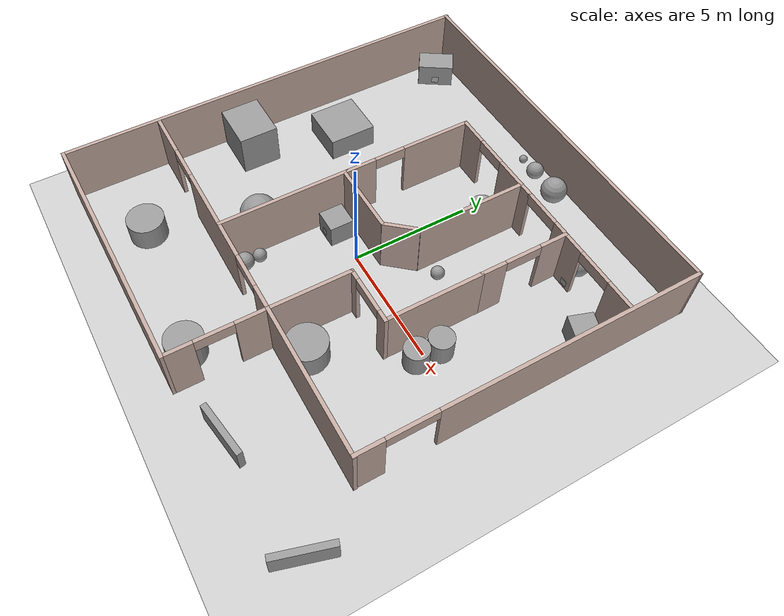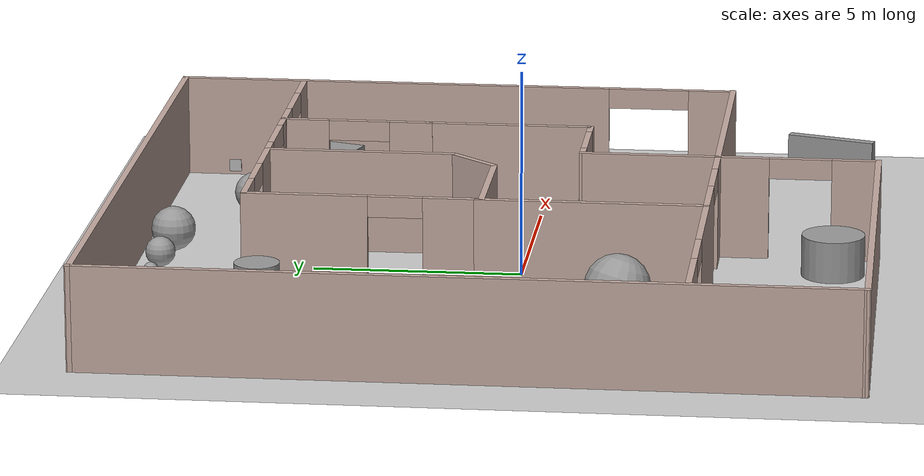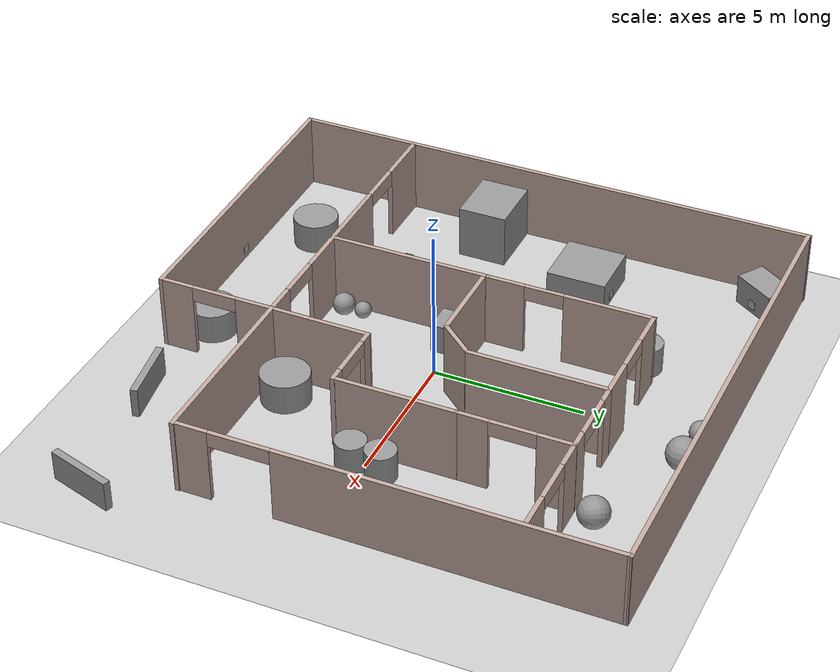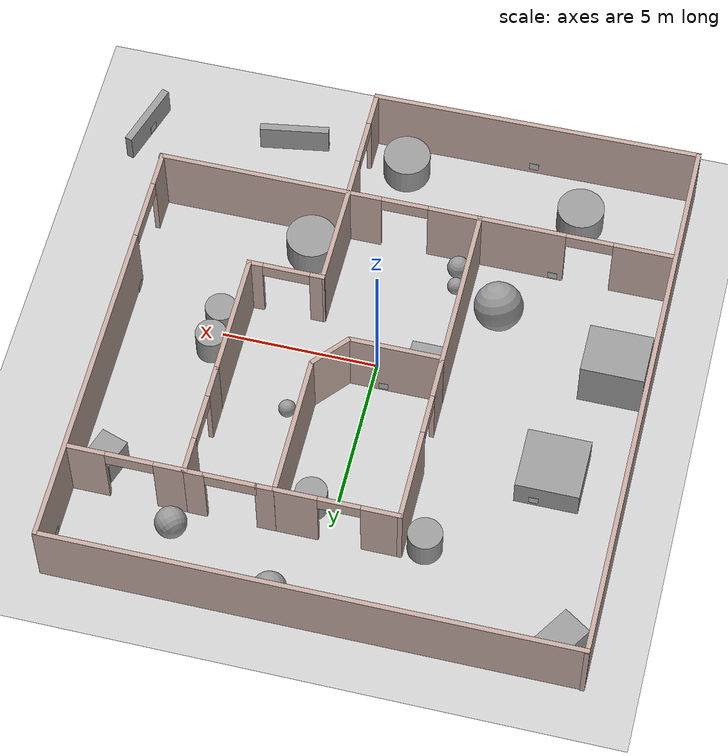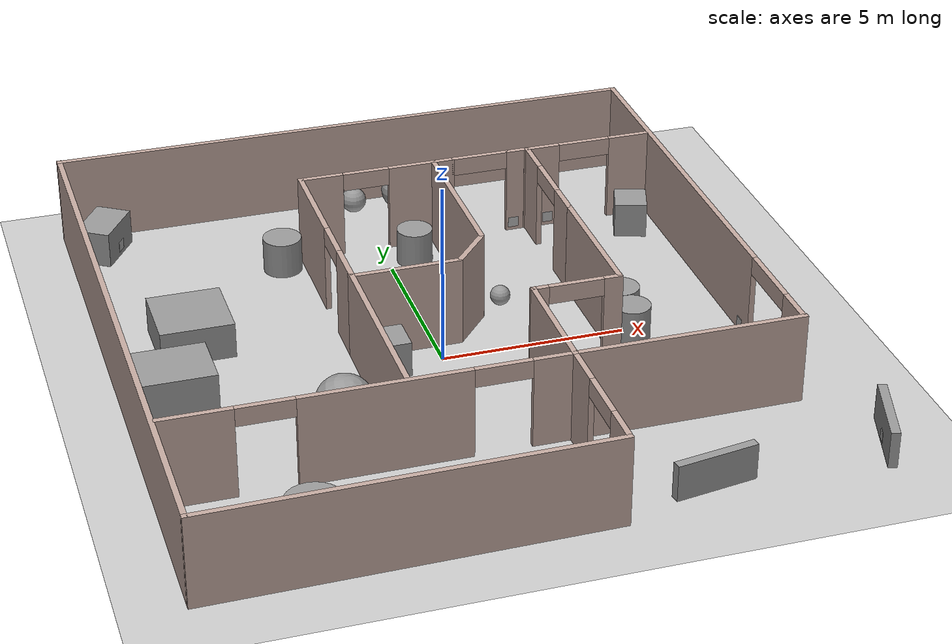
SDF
<sdf version="1.6">
 <world name="default">
  <light name="sun" type="directional">
   <pose>0 0 10 0 -0 0</pose>
   <diffuse>0.8 0.8 0.8 1</diffuse>
   <specular>0.2 0.2 0.2 1</specular>
   <attenuation>
    <range>1000</range>
    <constant>0.9</constant>
    <linear>0.01</linear>
    <quadratic>0.001</quadratic>
   </attenuation>
   <direction>-0.5 0.1 -0.9</direction>
  </light>
  <model name="ground_plane">
   <static>1</static>
   <link name="link">
    <collision name="collision">
     <geometry><plane><normal>0 0 1</normal><size>100 100</size></plane></geometry>
     <surface><friction><ode><mu>100</mu><mu2>50</mu2></ode></friction></surface>
    </collision>
    <visual name="visual">
     <cast_shadows>0</cast_shadows>
     <geometry><plane><normal>0 0 1</normal><size>100 100</size></plane></geometry>
     <material>
      <script><uri>file://media/materials/scripts/gazebo.material</uri><name>Gazebo/Grey</name></script>
     </material>
    </visual>
   </link>
  </model>
  <gravity>0 0 -9.8</gravity>
  <magnetic_field>6e-06 2.3e-05 -4.2e-05</magnetic_field>
  <atmosphere type="adiabatic"/>
  <physics name="default_physics" default="0" type="ode">
   <max_step_size>0.001</max_step_size>
   <real_time_factor>1</real_time_factor>
   <real_time_update_rate>1000</real_time_update_rate>
  </physics>
  <scene><ambient>0.4 0.4 0.4 1</ambient><background>0.7 0.7 0.7 1</background><shadows>1</shadows></scene>
  <audio><device>default</device></audio>
  <spherical_coordinates>
   <surface_model>EARTH_WGS84</surface_model>
   <latitude_deg>0</latitude_deg>
   <longitude_deg>0</longitude_deg>
   <elevation>0</elevation>
   <heading_deg>0</heading_deg>
  </spherical_coordinates>
  <model name="Apriltag36_11_00000">
   <link name="main">
    <visual name="main_Visual">
     <geometry><box><size>0.3 0.3 0.01</size></box></geometry>
     <material>
      <script>
       <uri>model://Apriltag36_11_00000/materials/scripts</uri>
       <uri>model://Apriltag36_11_00000/materials/textures</uri>
       <name>Apriltag36_11_00000</name>
      </script>
     </material>
    </visual>
   </link>
   <static>1</static>
   <pose>-1.57021 -0.566574 0.316551 1.5708 -0 0</pose>
  </model>
  <model name="Apriltag36_11_00001">
   <link name="main">
    <visual name="main_Visual">
     <geometry><box><size>0.3 0.3 0.01</size></box></geometry>
     <material>
      <script>
       <uri>model://Apriltag36_11_00001/materials/scripts</uri>
       <uri>model://Apriltag36_11_00001/materials/textures</uri>
       <name>Apriltag36_11_00001</name>
      </script>
     </material>
    </visual>
   </link>
   <static>1</static>
   <pose>3.97396 6.25837 0.243093 1.5708 -0 0</pose>
  </model>
  <model name="Apriltag36_11_00002">
   <link name="main">
    <visual name="main_Visual">
     <geometry><box><size>0.3 0.3 0.01</size></box></geometry>
     <material>
      <script>
       <uri>model://Apriltag36_11_00002/materials/scripts</uri>
       <uri>model://Apriltag36_11_00002/materials/textures</uri>
       <name>Apriltag36_11_00002</name>
      </script>
     </material>
    </visual>
   </link>
   <static>1</static>
   <pose>7.9597 -0.983528 0.288215 3.14159 -1.57079 3.14159</pose>
  </model>
  <model name="Apriltag36_11_00003">
   <link name="main">
    <visual name="main_Visual">
     <geometry><box><size>0.3 0.3 0.01</size></box></geometry>
     <material>
      <script>
       <uri>model://Apriltag36_11_00003/materials/scripts</uri>
       <uri>model://Apriltag36_11_00003/materials/textures</uri>
       <name>Apriltag36_11_00003</name>
      </script>
     </material>
    </visual>
   </link>
   <static>1</static>
   <pose>5.00792 6.24478 0.257866 1.5708 -0 0</pose>
  </model>
  <model name="Apriltag36_11_00004">
   <link name="main">
    <visual name="main_Visual">
     <geometry><box><size>0.3 0.3 0.01</size></box></geometry>
     <material>
      <script>
       <uri>model://Apriltag36_11_00004/materials/scripts</uri>
       <uri>model://Apriltag36_11_00004/materials/textures</uri>
       <name>Apriltag36_11_00004</name>
      </script>
     </material>
    </visual>
   </link>
   <static>1</static>
   <pose>-0.397155 0.800504 0.224863 -1.5708 0 0</pose>
  </model>
  <model name="Apriltag36_11_00005">
   <link name="main">
    <visual name="main_Visual">
     <geometry><box><size>0.3 0.3 0.01</size></box></geometry>
     <material>
      <script>
       <uri>model://Apriltag36_11_00005/materials/scripts</uri>
       <uri>model://Apriltag36_11_00005/materials/textures</uri>
       <name>Apriltag36_11_00005</name>
      </script>
     </material>
    </visual>
   </link>
   <static>1</static>
   <pose>-5.77552 3.72138 0.309475 -1.5708 0 0</pose>
  </model>
  <model name="Apriltag36_11_00006">
   <link name="main">
    <visual name="main_Visual">
     <geometry><box><size>0.3 0.3 0.01</size></box></geometry>
     <material>
      <script>
       <uri>model://Apriltag36_11_00006/materials/scripts</uri>
       <uri>model://Apriltag36_11_00006/materials/textures</uri>
       <name>Apriltag36_11_00006</name>
      </script>
     </material>
    </visual>
   </link>
   <static>1</static>
   <pose>-4.6719 -4.44536 0.215111 -1.5708 0 0</pose>
  </model>
  <model name="Apriltag36_11_00007">
   <link name="main">
    <visual name="main_Visual">
     <geometry><box><size>0.3 0.3 0.01</size></box></geometry>
     <material>
      <script>
       <uri>model://Apriltag36_11_00007/materials/scripts</uri>
       <uri>model://Apriltag36_11_00007/materials/textures</uri>
       <name>Apriltag36_11_00007</name>
      </script>
     </material>
    </visual>
   </link>
   <static>1</static>
   <pose>-7.08722 8.06862 0.297914 -2.57762 1.57079 3.13881</pose>
  </model>
  <model name="Apriltag36_11_00010">
   <link name="main">
    <visual name="main_Visual">
     <geometry><box><size>0.3 0.3 0.01</size></box></geometry>
     <material>
      <script>
       <uri>model://Apriltag36_11_00010/materials/scripts</uri>
       <uri>model://Apriltag36_11_00010/materials/textures</uri>
       <name>Apriltag36_11_00010</name>
      </script>
     </material>
    </visual>
   </link>
   <static>1</static>
   <pose>-3.24803 -8.3556 0.338631 -1.5708 0 0</pose>
  </model>
  <model name="unit_box">
   <pose>-1.50535 -0.067022 0.499995 0 -1e-05 0</pose>
   <link name="link">
    <inertial>
     <mass>1</mass>
     <inertia>
      <ixx>0.166667</ixx>
      <ixy>0</ixy>
      <ixz>0</ixz>
      <iyy>0.166667</iyy>
      <iyz>0</iyz>
      <izz>0.166667</izz>
     </inertia>
    </inertial>
    <collision name="collision"><geometry><box><size>1 1 1</size></box></geometry></collision>
    <visual name="visual">
     <geometry><box><size>1 1 1</size></box></geometry>
     <material>
      <script><name>Gazebo/Grey</name><uri>file://media/materials/scripts/gazebo.material</uri></script>
     </material>
    </visual>
   </link>
  </model>
  <model name="unit_cylinder">
   <pose>3.01103 -3.63468 0.499995 6e-06 -6e-06 -1.2e-05</pose>
   <link name="link">
    <inertial>
     <mass>1</mass>
     <inertia><ixx>0.145833</ixx><ixy>0</ixy><ixz>0</ixz><iyy>0.145833</iyy><iyz>0</iyz><izz>0.125</izz></inertia>
    </inertial>
    <collision name="collision">
     <geometry><cylinder><radius>0.80326</radius><length>1</length></cylinder></geometry>
    </collision>
    <visual name="visual">
     <geometry><cylinder><radius>0.80326</radius><length>1</length></cylinder></geometry>
     <material>
      <script><name>Gazebo/Grey</name><uri>file://media/materials/scripts/gazebo.material</uri></script>
     </material>
    </visual>
   </link>
  </model>
  <model name="unit_box_0">
   <pose>7.20629 5.34642 0.5 0 0 -0.320041</pose>
   <link name="link">
    <inertial>
     <mass>1</mass>
     <inertia>
      <ixx>0.166667</ixx>
      <ixy>0</ixy>
      <ixz>0</ixz>
      <iyy>0.166667</iyy>
      <iyz>0</iyz>
      <izz>0.166667</izz>
     </inertia>
    </inertial>
    <collision name="collision"><geometry><box><size>0.905691 1 1</size></box></geometry></collision>
    <visual name="visual">
     <geometry><box><size>0.905691 1 1</size></box></geometry>
     <material>
      <script><name>Gazebo/Grey</name><uri>file://media/materials/scripts/gazebo.material</uri></script>
     </material>
    </visual>
   </link>
  </model>
  <model name="unit_cylinder_0">
   <pose>5.12559 -0.383111 0.499996 5e-06 -2e-06 8.2e-05</pose>
   <link name="link">
    <inertial>
     <mass>1</mass>
     <inertia><ixx>0.145833</ixx><ixy>0</ixy><ixz>0</ixz><iyy>0.145833</iyy><iyz>0</iyz><izz>0.125</izz></inertia>
    </inertial>
    <collision name="collision">
     <geometry><cylinder><radius>0.5</radius><length>1</length></cylinder></geometry>
    </collision>
    <visual name="visual">
     <geometry><cylinder><radius>0.5</radius><length>1</length></cylinder></geometry>
     <material>
      <script><name>Gazebo/Grey</name><uri>file://media/materials/scripts/gazebo.material</uri></script>
     </material>
    </visual>
   </link>
  </model>
  <model name="unit_sphere">
   <pose>4.69867 7.10396 0.5 1.42269 -0.251788 0.775275</pose>
   <link name="link">
    <inertial>
     <mass>1</mass>
     <inertia><ixx>0.1</ixx><ixy>0</ixy><ixz>0</ixz><iyy>0.1</iyy><iyz>0</iyz><izz>0.1</izz></inertia>
    </inertial>
    <collision name="collision"><geometry><sphere><radius>0.5</radius></sphere></geometry></collision>
    <visual name="visual">
     <geometry><sphere><radius>0.5</radius></sphere></geometry>
     <material>
      <script><name>Gazebo/Grey</name><uri>file://media/materials/scripts/gazebo.material</uri></script>
     </material>
    </visual>
   </link>
  </model>
  <model name="unit_sphere_0">
   <pose>2.30869 2.29807 0.27459 0 -0 0</pose>
   <link name="link">
    <inertial>
     <mass>1</mass>
     <inertia><ixx>0.1</ixx><ixy>0</ixy><ixz>0</ixz><iyy>0.1</iyy><iyz>0</iyz><izz>0.1</izz></inertia>
    </inertial>
    <collision name="collision"><geometry><sphere><radius>0.27459</radius></sphere></geometry></collision>
    <visual name="visual">
     <geometry><sphere><radius>0.27459</radius></sphere></geometry>
     <material>
      <script><name>Gazebo/Grey</name><uri>file://media/materials/scripts/gazebo.material</uri></script>
     </material>
    </visual>
   </link>
  </model>
  <model name="unit_sphere_1">
   <pose>1.23479 8.58863 0.535665 0 -0 0</pose>
   <link name="link">
    <inertial>
     <mass>1</mass>
     <inertia><ixx>0.1</ixx><ixy>0</ixy><ixz>0</ixz><iyy>0.1</iyy><iyz>0</iyz><izz>0.1</izz></inertia>
    </inertial>
    <collision name="collision"><geometry><sphere><radius>0.535665</radius></sphere></geometry></collision>
    <visual name="visual">
     <geometry><sphere><radius>0.535665</radius></sphere></geometry>
     <material>
      <script><name>Gazebo/Grey</name><uri>file://media/materials/scripts/gazebo.material</uri></script>
     </material>
    </visual>
   </link>
  </model>
  <model name="unit_cylinder_1">
   <pose>0.760114 5.34321 0.499996 3e-06 1e-06 -0</pose>
   <link name="link">
    <inertial>
     <mass>1</mass>
     <inertia><ixx>0.145833</ixx><ixy>0</ixy><ixz>0</ixz><iyy>0.145833</iyy><iyz>0</iyz><izz>0.125</izz></inertia>
    </inertial>
    <collision name="collision">
     <geometry><cylinder><radius>0.5</radius><length>1</length></cylinder></geometry>
    </collision>
    <visual name="visual">
     <geometry><cylinder><radius>0.5</radius><length>1</length></cylinder></geometry>
     <material>
      <script><name>Gazebo/Grey</name><uri>file://media/materials/scripts/gazebo.material</uri></script>
     </material>
    </visual>
   </link>
  </model>
  <model name="unit_box_1">
   <pose>-6.16148 2.69722 0.499986 1.4e-05 -0 -5e-06</pose>
   <link name="link">
    <inertial>
     <mass>1</mass>
     <inertia>
      <ixx>0.166667</ixx>
      <ixy>0</ixy>
      <ixz>0</ixz>
      <iyy>0.166667</iyy>
      <iyz>0</iyz>
      <izz>0.166667</izz>
     </inertia>
    </inertial>
    <collision name="collision"><geometry><box><size>2 2 1</size></box></geometry></collision>
    <visual name="visual">
     <geometry><box><size>2 2 1</size></box></geometry>
     <material>
      <script><name>Gazebo/Grey</name><uri>file://media/materials/scripts/gazebo.material</uri></script>
     </material>
    </visual>
   </link>
  </model>
  <model name="unit_box_1_clone">
   <pose>-7.32637 -1.09862 0.902183 0 -0 -9e-06</pose>
   <link name="link">
    <inertial>
     <mass>1</mass>
     <inertia>
      <ixx>0.166667</ixx>
      <ixy>0</ixy>
      <ixz>0</ixz>
      <iyy>0.166667</iyy>
      <iyz>0</iyz>
      <izz>0.166667</izz>
     </inertia>
    </inertial>
    <collision name="collision"><geometry><box><size>2 1.6321 1.80437</size></box></geometry></collision>
    <visual name="visual">
     <geometry><box><size>2 1.6321 1.80437</size></box></geometry>
     <material>
      <script><name>Gazebo/Grey</name><uri>file://media/materials/scripts/gazebo.material</uri></script>
     </material>
    </visual>
   </link>
  </model>
  <model name="unit_cylinder_2">
   <pose>-5.11308 -6.66758 0.499996 5e-06 5e-06 -3e-06</pose>
   <link name="link">
    <inertial>
     <mass>1</mass>
     <inertia><ixx>0.145833</ixx><ixy>0</ixy><ixz>0</ixz><iyy>0.145833</iyy><iyz>0</iyz><izz>0.125</izz></inertia>
    </inertial>
    <collision name="collision">
     <geometry><cylinder><radius>0.75481</radius><length>1</length></cylinder></geometry>
    </collision>
    <visual name="visual">
     <geometry><cylinder><radius>0.75481</radius><length>1</length></cylinder></geometry>
     <material>
      <script><name>Gazebo/Grey</name><uri>file://media/materials/scripts/gazebo.material</uri></script>
     </material>
    </visual>
   </link>
  </model>
  <model name="unit_cylinder_2_clone">
   <pose>0.767807 -7.38529 0.499996 5e-06 5e-06 -3e-06</pose>
   <link name="link">
    <inertial>
     <mass>1</mass>
     <inertia><ixx>0.145833</ixx><ixy>0</ixy><ixz>0</ixz><iyy>0.145833</iyy><iyz>0</iyz><izz>0.125</izz></inertia>
    </inertial>
    <collision name="collision">
     <geometry><cylinder><radius>0.75481</radius><length>1</length></cylinder></geometry>
    </collision>
    <visual name="visual">
     <geometry><cylinder><radius>0.75481</radius><length>1</length></cylinder></geometry>
     <material>
      <script><name>Gazebo/Grey</name><uri>file://media/materials/scripts/gazebo.material</uri></script>
     </material>
    </visual>
   </link>
  </model>
  <model name="unit_cylinder_3">
   <pose>-2.90641 5.94109 0.499996 4e-06 4e-06 -1e-06</pose>
   <link name="link">
    <inertial>
     <mass>1</mass>
     <inertia><ixx>0.145833</ixx><ixy>0</ixy><ixz>0</ixz><iyy>0.145833</iyy><iyz>0</iyz><izz>0.125</izz></inertia>
    </inertial>
    <collision name="collision">
     <geometry><cylinder><radius>0.54008</radius><length>1</length></cylinder></geometry>
    </collision>
    <visual name="visual">
     <geometry><cylinder><radius>0.54008</radius><length>1</length></cylinder></geometry>
     <material>
      <script><name>Gazebo/Grey</name><uri>file://media/materials/scripts/gazebo.material</uri></script>
     </material>
    </visual>
   </link>
  </model>
  <model name="unit_box_2">
   <pose>-7.51786 8.34872 0.5 0 -0 -0.57762</pose>
   <link name="link">
    <inertial>
     <mass>1</mass>
     <inertia>
      <ixx>0.166667</ixx>
      <ixy>0</ixy>
      <ixz>0</ixz>
      <iyy>0.166667</iyy>
      <iyz>0</iyz>
      <izz>0.166667</izz>
     </inertia>
    </inertial>
    <collision name="collision"><geometry><box><size>1 1.52871 1</size></box></geometry></collision>
    <visual name="visual">
     <geometry><box><size>1 1.52871 1</size></box></geometry>
     <material>
      <script><name>Gazebo/Grey</name><uri>file://media/materials/scripts/gazebo.material</uri></script>
     </material>
    </visual>
   </link>
  </model>
  <model name="unit_box_3">
   <pose>4.5781 -7.57648 0.499969 1e-06 2.8e-05 0.159962</pose>
   <link name="link">
    <inertial>
     <mass>1</mass>
     <inertia>
      <ixx>0.166667</ixx>
      <ixy>0</ixy>
      <ixz>0</ixz>
      <iyy>0.166667</iyy>
      <iyz>0</iyz>
      <izz>0.166667</izz>
     </inertia>
    </inertial>
    <collision name="collision"><geometry><box><size>2.24418 0.240328 1</size></box></geometry></collision>
    <visual name="visual">
     <geometry><box><size>2.24418 0.240328 1</size></box></geometry>
     <material>
      <script><name>Gazebo/Grey</name><uri>file://media/materials/scripts/gazebo.material</uri></script>
     </material>
    </visual>
   </link>
  </model>
  <model name="unit_box_3_clone">
   <pose>9.39191 -6.9847 0.49997 -1e-06 2.7e-05 1.2743</pose>
   <link name="link">
    <inertial>
     <mass>1</mass>
     <inertia>
      <ixx>0.166667</ixx>
      <ixy>0</ixy>
      <ixz>0</ixz>
      <iyy>0.166667</iyy>
      <iyz>0</iyz>
      <izz>0.166667</izz>
     </inertia>
    </inertial>
    <collision name="collision"><geometry><box><size>2.24418 0.240328 1</size></box></geometry></collision>
    <visual name="visual">
     <geometry><box><size>2.24418 0.240328 1</size></box></geometry>
     <material>
      <script><name>Gazebo/Grey</name><uri>file://media/materials/scripts/gazebo.material</uri></script>
     </material>
    </visual>
   </link>
  </model>
  <model name="unit_sphere_2">
   <pose>-3.3154 -2.55999 0.786618 0.26742 0.258441 -0.030283</pose>
   <link name="link">
    <inertial>
     <mass>1</mass>
     <inertia><ixx>0.1</ixx><ixy>0</ixy><ixz>0</ixz><iyy>0.1</iyy><iyz>0</iyz><izz>0.1</izz></inertia>
    </inertial>
    <collision name="collision"><geometry><sphere><radius>0.786618</radius></sphere></geometry></collision>
    <visual name="visual">
     <geometry><sphere><radius>0.786618</radius></sphere></geometry>
     <material>
      <script><name>Gazebo/Grey</name><uri>file://media/materials/scripts/gazebo.material</uri></script>
     </material>
    </visual>
   </link>
  </model>
  <model name="Apriltag36_11_00008">
   <link name="main">
    <visual name="main_Visual">
     <geometry><box><size>0.3 0.3 0.01</size></box></geometry>
     <material>
      <script>
       <uri>model://Apriltag36_11_00008/materials/scripts</uri>
       <uri>model://Apriltag36_11_00008/materials/textures</uri>
       <name>Apriltag36_11_00008</name>
      </script>
     </material>
    </visual>
   </link>
   <static>1</static>
   <pose>9.23593 -7.03166 0.262671 2.83789 -1.57079 -3.14025</pose>
  </model>
  <model name="Apriltag36_11_00009">
   <link name="main">
    <visual name="main_Visual">
     <geometry><box><size>0.3 0.3 0.01</size></box></geometry>
     <material>
      <script>
       <uri>model://Apriltag36_11_00009/materials/scripts</uri>
       <uri>model://Apriltag36_11_00009/materials/textures</uri>
       <name>Apriltag36_11_00009</name>
      </script>
     </material>
    </visual>
   </link>
   <static>1</static>
   <pose>8.00777 8.10684 0.233187 3.14159 -1.57079 3.14159</pose>
  </model>
  <model name="unit_sphere_3">
   <pose>-0.133786 8.68812 0.359436 0 -0 0</pose>
   <link name="link">
    <inertial>
     <mass>1</mass>
     <inertia><ixx>0.1</ixx><ixy>0</ixy><ixz>0</ixz><iyy>0.1</iyy><iyz>0</iyz><izz>0.1</izz></inertia>
    </inertial>
    <collision name="collision"><geometry><sphere><radius>0.359436</radius></sphere></geometry></collision>
    <visual name="visual">
     <geometry><sphere><radius>0.359436</radius></sphere></geometry>
     <material>
      <script><name>Gazebo/Grey</name><uri>file://media/materials/scripts/gazebo.material</uri></script>
     </material>
    </visual>
   </link>
  </model>
  <model name="unit_sphere_4">
   <pose>-1.0379 8.7732 0.175664 0 -0 0</pose>
   <link name="link">
    <inertial>
     <mass>1</mass>
     <inertia><ixx>0.1</ixx><ixy>0</ixy><ixz>0</ixz><iyy>0.1</iyy><iyz>0</iyz><izz>0.1</izz></inertia>
    </inertial>
    <collision name="collision"><geometry><sphere><radius>0.175664</radius></sphere></geometry></collision>
    <visual name="visual">
     <geometry><sphere><radius>0.175664</radius></sphere></geometry>
     <material>
      <script><name>Gazebo/Grey</name><uri>file://media/materials/scripts/gazebo.material</uri></script>
     </material>
    </visual>
   </link>
  </model>
  <model name="House3">
   <link name="Wall_0">
    <pose>1.97583 -8.25887 0 0 -0 0</pose>
    <visual name="Wall_0_Visual_0">
     <pose>-6.4191 0 1.25 0 -0 0</pose>
     <geometry><box><size>1.18181 0.15 2.5</size></box></geometry>
     <material>
      <script><uri>file://media/materials/scripts/gazebo.material</uri><name>Gazebo/Grey</name></script>
      <ambient>0.760784 0.662745 0.627451 1</ambient>
     </material>
     <meta><layer>0</layer></meta>
    </visual>
    <visual name="Wall_0_Visual_1">
     <pose>1.5909 0 1.25 0 -0 0</pose>
     <geometry><box><size>10.8382 0.15 2.5</size></box></geometry>
     <material>
      <script><uri>file://media/materials/scripts/gazebo.material</uri><name>Gazebo/Grey</name></script>
      <ambient>0.760784 0.662745 0.627451 1</ambient>
     </material>
     <meta><layer>0</layer></meta>
    </visual>
    <visual name="Wall_0_Visual_2">
     <pose>-4.82819 0 2.25 0 -0 0</pose>
     <geometry><box><size>2 0.15 0.5</size></box></geometry>
     <material>
      <script><uri>file://media/materials/scripts/gazebo.material</uri><name>Gazebo/Grey</name></script>
      <ambient>0.760784 0.662745 0.627451 1</ambient>
     </material>
     <meta><layer>0</layer></meta>
    </visual>
    <collision name="Wall_0_Collision_0">
     <pose>-6.4191 0 1.25 0 -0 0</pose>
     <geometry><box><size>1.18181 0.15 2.5</size></box></geometry>
     <surface>
      <friction>
       <ode><mu>1</mu><mu2>1</mu2><fdir1>0 0 0</fdir1><slip1>0</slip1><slip2>0</slip2></ode>
       <torsional>
        <coefficient>1</coefficient>
        <patch_radius>0</patch_radius>
        <surface_radius>0</surface_radius>
        <use_patch_radius>1</use_patch_radius>
        <ode><slip>0</slip></ode>
       </torsional>
      </friction>
      <bounce><restitution_coefficient>0</restitution_coefficient><threshold>1e+06</threshold></bounce>
      <contact>
       <collide_without_contact>0</collide_without_contact>
       <collide_without_contact_bitmask>1</collide_without_contact_bitmask>
       <collide_bitmask>1</collide_bitmask>
       <ode>
        <soft_cfm>0</soft_cfm>
        <soft_erp>0.2</soft_erp>
        <kp>1e+13</kp>
        <kd>1</kd>
        <max_vel>0.01</max_vel>
        <min_depth>0</min_depth>
       </ode>
       <bullet>
        <split_impulse>1</split_impulse>
        <split_impulse_penetration_threshold>-0.01</split_impulse_penetration_threshold>
        <soft_cfm>0</soft_cfm>
        <soft_erp>0.2</soft_erp>
        <kp>1e+13</kp>
        <kd>1</kd>
       </bullet>
      </contact>
     </surface>
    </collision>
    <collision name="Wall_0_Collision_1">
     <pose>1.5909 0 1.25 0 -0 0</pose>
     <geometry><box><size>10.8382 0.15 2.5</size></box></geometry>
     <surface>
      <friction>
       <ode><mu>1</mu><mu2>1</mu2><fdir1>0 0 0</fdir1><slip1>0</slip1><slip2>0</slip2></ode>
       <torsional>
        <coefficient>1</coefficient>
        <patch_radius>0</patch_radius>
        <surface_radius>0</surface_radius>
        <use_patch_radius>1</use_patch_radius>
        <ode><slip>0</slip></ode>
       </torsional>
      </friction>
      <bounce><restitution_coefficient>0</restitution_coefficient><threshold>1e+06</threshold></bounce>
      <contact>
       <collide_without_contact>0</collide_without_contact>
       <collide_without_contact_bitmask>1</collide_without_contact_bitmask>
       <collide_bitmask>1</collide_bitmask>
       <ode>
        <soft_cfm>0</soft_cfm>
        <soft_erp>0.2</soft_erp>
        <kp>1e+13</kp>
        <kd>1</kd>
        <max_vel>0.01</max_vel>
        <min_depth>0</min_depth>
       </ode>
       <bullet>
        <split_impulse>1</split_impulse>
        <split_impulse_penetration_threshold>-0.01</split_impulse_penetration_threshold>
        <soft_cfm>0</soft_cfm>
        <soft_erp>0.2</soft_erp>
        <kp>1e+13</kp>
        <kd>1</kd>
       </bullet>
      </contact>
     </surface>
    </collision>
    <collision name="Wall_0_Collision_2">
     <pose>-4.82819 0 2.25 0 -0 0</pose>
     <geometry><box><size>2 0.15 0.5</size></box></geometry>
     <surface>
      <friction>
       <ode><mu>1</mu><mu2>1</mu2><fdir1>0 0 0</fdir1><slip1>0</slip1><slip2>0</slip2></ode>
       <torsional>
        <coefficient>1</coefficient>
        <patch_radius>0</patch_radius>
        <surface_radius>0</surface_radius>
        <use_patch_radius>1</use_patch_radius>
        <ode><slip>0</slip></ode>
       </torsional>
      </friction>
      <bounce><restitution_coefficient>0</restitution_coefficient><threshold>1e+06</threshold></bounce>
      <contact>
       <collide_without_contact>0</collide_without_contact>
       <collide_without_contact_bitmask>1</collide_without_contact_bitmask>
       <collide_bitmask>1</collide_bitmask>
       <ode>
        <soft_cfm>0</soft_cfm>
        <soft_erp>0.2</soft_erp>
        <kp>1e+13</kp>
        <kd>1</kd>
        <max_vel>0.01</max_vel>
        <min_depth>0</min_depth>
       </ode>
       <bullet>
        <split_impulse>1</split_impulse>
        <split_impulse_penetration_threshold>-0.01</split_impulse_penetration_threshold>
        <soft_cfm>0</soft_cfm>
        <soft_erp>0.2</soft_erp>
        <kp>1e+13</kp>
        <kd>1</kd>
       </bullet>
      </contact>
     </surface>
    </collision>
   </link>
   <link name="Wall_1">
    <pose>8.92109 0.01342 0 0 -0 1.57168</pose>
    <visual name="Wall_1_Visual">
     <pose>0 0 1.25 0 -0 0</pose>
     <geometry><box><size>16.6946 0.15 2.5</size></box></geometry>
     <material>
      <script><uri>file://media/materials/scripts/gazebo.material</uri><name>Gazebo/Grey</name></script>
      <ambient>0.760784 0.662745 0.627451 1</ambient>
     </material>
     <meta><layer>0</layer></meta>
    </visual>
    <collision name="Wall_1_Collision">
     <pose>0 0 1.25 0 -0 0</pose>
     <geometry><box><size>16.6946 0.15 2.5</size></box></geometry>
     <surface>
      <friction>
       <ode><mu>1</mu><mu2>1</mu2><fdir1>0 0 0</fdir1><slip1>0</slip1><slip2>0</slip2></ode>
       <torsional>
        <coefficient>1</coefficient>
        <patch_radius>0</patch_radius>
        <surface_radius>0</surface_radius>
        <use_patch_radius>1</use_patch_radius>
        <ode><slip>0</slip></ode>
       </torsional>
      </friction>
      <bounce><restitution_coefficient>0</restitution_coefficient><threshold>1e+06</threshold></bounce>
      <contact>
       <collide_without_contact>0</collide_without_contact>
       <collide_without_contact_bitmask>1</collide_without_contact_bitmask>
       <collide_bitmask>1</collide_bitmask>
       <ode>
        <soft_cfm>0</soft_cfm>
        <soft_erp>0.2</soft_erp>
        <kp>1e+13</kp>
        <kd>1</kd>
        <max_vel>0.01</max_vel>
        <min_depth>0</min_depth>
       </ode>
       <bullet>
        <split_impulse>1</split_impulse>
        <split_impulse_penetration_threshold>-0.01</split_impulse_penetration_threshold>
        <soft_cfm>0</soft_cfm>
        <soft_erp>0.2</soft_erp>
        <kp>1e+13</kp>
        <kd>1</kd>
       </bullet>
      </contact>
     </surface>
    </collision>
   </link>
   <link name="Wall_10">
    <pose>2.08861 -4.55032 0 0 -0 0</pose>
    <inertial>
     <mass>1</mass>
     <inertia><ixx>1</ixx><ixy>0</ixy><ixz>0</ixz><iyy>1</iyy><iyz>0</iyz><izz>1</izz></inertia>
    </inertial>
    <visual name="Wall_10_Visual">
     <pose>-1.8 0 1.25 0 -0 0</pose>
     <geometry><box><size>4 0.15 2.5</size></box></geometry>
     <material>
      <script><uri>file://media/materials/scripts/gazebo.material</uri><name>Gazebo/Grey</name></script>
      <ambient>0.761 0.663 0.627 1</ambient>
      <shader type="vertex"><normal_map>__default__</normal_map></shader>
      <diffuse>0.7 0.7 0.7 1</diffuse>
      <specular>0.01 0.01 0.01 1</specular>
      <emissive>0 0 0 1</emissive>
     </material>
     <meta><layer>0</layer></meta>
    </visual>
    <collision name="Wall_10_Collision">
     <pose>-1.8 0 1.25 0 -0 0</pose>
     <geometry><box><size>4 0.15 2.5</size></box></geometry>
     <surface>
      <friction>
       <ode><mu>1</mu><mu2>1</mu2><fdir1>0 0 0</fdir1><slip1>0</slip1><slip2>0</slip2></ode>
       <torsional>
        <coefficient>1</coefficient>
        <patch_radius>0</patch_radius>
        <surface_radius>0</surface_radius>
        <use_patch_radius>1</use_patch_radius>
        <ode><slip>0</slip></ode>
       </torsional>
      </friction>
      <bounce><restitution_coefficient>0</restitution_coefficient><threshold>1e+06</threshold></bounce>
      <contact>
       <collide_without_contact>0</collide_without_contact>
       <collide_without_contact_bitmask>1</collide_without_contact_bitmask>
       <collide_bitmask>1</collide_bitmask>
       <ode>
        <soft_cfm>0</soft_cfm>
        <soft_erp>0.2</soft_erp>
        <kp>1e+13</kp>
        <kd>1</kd>
        <max_vel>0.01</max_vel>
        <min_depth>0</min_depth>
       </ode>
       <bullet>
        <split_impulse>1</split_impulse>
        <split_impulse_penetration_threshold>-0.01</split_impulse_penetration_threshold>
        <soft_cfm>0</soft_cfm>
        <soft_erp>0.2</soft_erp>
        <kp>1e+13</kp>
        <kd>1</kd>
       </bullet>
      </contact>
     </surface>
    </collision>
   </link>
   <link name="Wall_13">
    <pose>-4.97017 2.98867 0 0 -0 1.5708</pose>
    <visual name="Wall_13_Visual_0">
     <pose>-4.67446 0 1.25 0 -0 0</pose>
     <geometry><box><size>1.15108 0.15 2.5</size></box></geometry>
     <material>
      <script><uri>file://media/materials/scripts/gazebo.material</uri><name>Gazebo/Grey</name></script>
      <ambient>0.760784 0.662745 0.627451 1</ambient>
     </material>
     <meta><layer>0</layer></meta>
    </visual>
    <visual name="Wall_13_Visual_1">
     <pose>-0.385408 0 1.25 0 -0 0</pose>
     <geometry><box><size>4.42703 0.15 2.5</size></box></geometry>
     <material>
      <script><uri>file://media/materials/scripts/gazebo.material</uri><name>Gazebo/Grey</name></script>
      <ambient>0.760784 0.662745 0.627451 1</ambient>
     </material>
     <meta><layer>0</layer></meta>
    </visual>
    <visual name="Wall_13_Visual_2">
     <pose>4.28906 0 1.25 0 -0 0</pose>
     <geometry><box><size>1.92189 0.15 2.5</size></box></geometry>
     <material>
      <script><uri>file://media/materials/scripts/gazebo.material</uri><name>Gazebo/Grey</name></script>
      <ambient>0.760784 0.662745 0.627451 1</ambient>
     </material>
     <meta><layer>0</layer></meta>
    </visual>
    <visual name="Wall_13_Visual_3">
     <pose>-3.34892 0 2.25 0 -0 0</pose>
     <geometry><box><size>1.5 0.15 0.5</size></box></geometry>
     <material>
      <script><uri>file://media/materials/scripts/gazebo.material</uri><name>Gazebo/Grey</name></script>
      <ambient>0.760784 0.662745 0.627451 1</ambient>
     </material>
     <meta><layer>0</layer></meta>
    </visual>
    <visual name="Wall_13_Visual_4">
     <pose>2.57811 0 2.25 0 -0 0</pose>
     <geometry><box><size>1.5 0.15 0.5</size></box></geometry>
     <material>
      <script><uri>file://media/materials/scripts/gazebo.material</uri><name>Gazebo/Grey</name></script>
      <ambient>0.760784 0.662745 0.627451 1</ambient>
     </material>
     <meta><layer>0</layer></meta>
    </visual>
    <collision name="Wall_13_Collision_0">
     <pose>-4.67446 0 1.25 0 -0 0</pose>
     <geometry><box><size>1.15108 0.15 2.5</size></box></geometry>
     <surface>
      <friction>
       <ode><mu>1</mu><mu2>1</mu2><fdir1>0 0 0</fdir1><slip1>0</slip1><slip2>0</slip2></ode>
       <torsional>
        <coefficient>1</coefficient>
        <patch_radius>0</patch_radius>
        <surface_radius>0</surface_radius>
        <use_patch_radius>1</use_patch_radius>
        <ode><slip>0</slip></ode>
       </torsional>
      </friction>
      <bounce><restitution_coefficient>0</restitution_coefficient><threshold>1e+06</threshold></bounce>
      <contact>
       <collide_without_contact>0</collide_without_contact>
       <collide_without_contact_bitmask>1</collide_without_contact_bitmask>
       <collide_bitmask>1</collide_bitmask>
       <ode>
        <soft_cfm>0</soft_cfm>
        <soft_erp>0.2</soft_erp>
        <kp>1e+13</kp>
        <kd>1</kd>
        <max_vel>0.01</max_vel>
        <min_depth>0</min_depth>
       </ode>
       <bullet>
        <split_impulse>1</split_impulse>
        <split_impulse_penetration_threshold>-0.01</split_impulse_penetration_threshold>
        <soft_cfm>0</soft_cfm>
        <soft_erp>0.2</soft_erp>
        <kp>1e+13</kp>
        <kd>1</kd>
       </bullet>
      </contact>
     </surface>
    </collision>
    <collision name="Wall_13_Collision_1">
     <pose>-0.385408 0 1.25 0 -0 0</pose>
     <geometry><box><size>4.42703 0.15 2.5</size></box></geometry>
     <surface>
      <friction>
       <ode><mu>1</mu><mu2>1</mu2><fdir1>0 0 0</fdir1><slip1>0</slip1><slip2>0</slip2></ode>
       <torsional>
        <coefficient>1</coefficient>
        <patch_radius>0</patch_radius>
        <surface_radius>0</surface_radius>
        <use_patch_radius>1</use_patch_radius>
        <ode><slip>0</slip></ode>
       </torsional>
      </friction>
      <bounce><restitution_coefficient>0</restitution_coefficient><threshold>1e+06</threshold></bounce>
      <contact>
       <collide_without_contact>0</collide_without_contact>
       <collide_without_contact_bitmask>1</collide_without_contact_bitmask>
       <collide_bitmask>1</collide_bitmask>
       <ode>
        <soft_cfm>0</soft_cfm>
        <soft_erp>0.2</soft_erp>
        <kp>1e+13</kp>
        <kd>1</kd>
        <max_vel>0.01</max_vel>
        <min_depth>0</min_depth>
       </ode>
       <bullet>
        <split_impulse>1</split_impulse>
        <split_impulse_penetration_threshold>-0.01</split_impulse_penetration_threshold>
        <soft_cfm>0</soft_cfm>
        <soft_erp>0.2</soft_erp>
        <kp>1e+13</kp>
        <kd>1</kd>
       </bullet>
      </contact>
     </surface>
    </collision>
    <collision name="Wall_13_Collision_2">
     <pose>4.28906 0 1.25 0 -0 0</pose>
     <geometry><box><size>1.92189 0.15 2.5</size></box></geometry>
     <surface>
      <friction>
       <ode><mu>1</mu><mu2>1</mu2><fdir1>0 0 0</fdir1><slip1>0</slip1><slip2>0</slip2></ode>
       <torsional>
        <coefficient>1</coefficient>
        <patch_radius>0</patch_radius>
        <surface_radius>0</surface_radius>
        <use_patch_radius>1</use_patch_radius>
        <ode><slip>0</slip></ode>
       </torsional>
      </friction>
      <bounce><restitution_coefficient>0</restitution_coefficient><threshold>1e+06</threshold></bounce>
      <contact>
       <collide_without_contact>0</collide_without_contact>
       <collide_without_contact_bitmask>1</collide_without_contact_bitmask>
       <collide_bitmask>1</collide_bitmask>
       <ode>
        <soft_cfm>0</soft_cfm>
        <soft_erp>0.2</soft_erp>
        <kp>1e+13</kp>
        <kd>1</kd>
        <max_vel>0.01</max_vel>
        <min_depth>0</min_depth>
       </ode>
       <bullet>
        <split_impulse>1</split_impulse>
        <split_impulse_penetration_threshold>-0.01</split_impulse_penetration_threshold>
        <soft_cfm>0</soft_cfm>
        <soft_erp>0.2</soft_erp>
        <kp>1e+13</kp>
        <kd>1</kd>
       </bullet>
      </contact>
     </surface>
    </collision>
    <collision name="Wall_13_Collision_3">
     <pose>-3.34892 0 2.25 0 -0 0</pose>
     <geometry><box><size>1.5 0.15 0.5</size></box></geometry>
     <surface>
      <friction>
       <ode><mu>1</mu><mu2>1</mu2><fdir1>0 0 0</fdir1><slip1>0</slip1><slip2>0</slip2></ode>
       <torsional>
        <coefficient>1</coefficient>
        <patch_radius>0</patch_radius>
        <surface_radius>0</surface_radius>
        <use_patch_radius>1</use_patch_radius>
        <ode><slip>0</slip></ode>
       </torsional>
      </friction>
      <bounce><restitution_coefficient>0</restitution_coefficient><threshold>1e+06</threshold></bounce>
      <contact>
       <collide_without_contact>0</collide_without_contact>
       <collide_without_contact_bitmask>1</collide_without_contact_bitmask>
       <collide_bitmask>1</collide_bitmask>
       <ode>
        <soft_cfm>0</soft_cfm>
        <soft_erp>0.2</soft_erp>
        <kp>1e+13</kp>
        <kd>1</kd>
        <max_vel>0.01</max_vel>
        <min_depth>0</min_depth>
       </ode>
       <bullet>
        <split_impulse>1</split_impulse>
        <split_impulse_penetration_threshold>-0.01</split_impulse_penetration_threshold>
        <soft_cfm>0</soft_cfm>
        <soft_erp>0.2</soft_erp>
        <kp>1e+13</kp>
        <kd>1</kd>
       </bullet>
      </contact>
     </surface>
    </collision>
    <collision name="Wall_13_Collision_4">
     <pose>2.57811 0 2.25 0 -0 0</pose>
     <geometry><box><size>1.5 0.15 0.5</size></box></geometry>
     <surface>
      <friction>
       <ode><mu>1</mu><mu2>1</mu2><fdir1>0 0 0</fdir1><slip1>0</slip1><slip2>0</slip2></ode>
       <torsional>
        <coefficient>1</coefficient>
        <patch_radius>0</patch_radius>
        <surface_radius>0</surface_radius>
        <use_patch_radius>1</use_patch_radius>
        <ode><slip>0</slip></ode>
       </torsional>
      </friction>
      <bounce><restitution_coefficient>0</restitution_coefficient><threshold>1e+06</threshold></bounce>
      <contact>
       <collide_without_contact>0</collide_without_contact>
       <collide_without_contact_bitmask>1</collide_without_contact_bitmask>
       <collide_bitmask>1</collide_bitmask>
       <ode>
        <soft_cfm>0</soft_cfm>
        <soft_erp>0.2</soft_erp>
        <kp>1e+13</kp>
        <kd>1</kd>
        <max_vel>0.01</max_vel>
        <min_depth>0</min_depth>
       </ode>
       <bullet>
        <split_impulse>1</split_impulse>
        <split_impulse_penetration_threshold>-0.01</split_impulse_penetration_threshold>
        <soft_cfm>0</soft_cfm>
        <soft_erp>0.2</soft_erp>
        <kp>1e+13</kp>
        <kd>1</kd>
       </bullet>
      </contact>
     </surface>
    </collision>
   </link>
   <link name="Wall_15">
    <pose>5.88971 -6.3218 0 0 0 -1.5708</pose>
    <visual name="Wall_15_Visual_0">
     <pose>-1.34561 0 1.25 0 -0 0</pose>
     <geometry><box><size>1.05878 0.15 2.5</size></box></geometry>
     <material>
      <script><uri>file://media/materials/scripts/gazebo.material</uri><name>Gazebo/Grey</name></script>
      <ambient>0.760784 0.662745 0.627451 1</ambient>
     </material>
     <meta><layer>0</layer></meta>
    </visual>
    <visual name="Wall_15_Visual_1">
     <pose>1.27939 0 1.25 0 -0 0</pose>
     <geometry><box><size>1.19122 0.15 2.5</size></box></geometry>
     <material>
      <script><uri>file://media/materials/scripts/gazebo.material</uri><name>Gazebo/Grey</name></script>
      <ambient>0.760784 0.662745 0.627451 1</ambient>
     </material>
     <meta><layer>0</layer></meta>
    </visual>
    <visual name="Wall_15_Visual_2">
     <pose>-0.06622 0 2.25 0 -0 0</pose>
     <geometry><box><size>1.5 0.15 0.5</size></box></geometry>
     <material>
      <script><uri>file://media/materials/scripts/gazebo.material</uri><name>Gazebo/Grey</name></script>
      <ambient>0.760784 0.662745 0.627451 1</ambient>
     </material>
     <meta><layer>0</layer></meta>
    </visual>
    <collision name="Wall_15_Collision_0">
     <pose>-1.34561 0 1.25 0 -0 0</pose>
     <geometry><box><size>1.05878 0.15 2.5</size></box></geometry>
     <surface>
      <friction>
       <ode><mu>1</mu><mu2>1</mu2><fdir1>0 0 0</fdir1><slip1>0</slip1><slip2>0</slip2></ode>
       <torsional>
        <coefficient>1</coefficient>
        <patch_radius>0</patch_radius>
        <surface_radius>0</surface_radius>
        <use_patch_radius>1</use_patch_radius>
        <ode><slip>0</slip></ode>
       </torsional>
      </friction>
      <bounce><restitution_coefficient>0</restitution_coefficient><threshold>1e+06</threshold></bounce>
      <contact>
       <collide_without_contact>0</collide_without_contact>
       <collide_without_contact_bitmask>1</collide_without_contact_bitmask>
       <collide_bitmask>1</collide_bitmask>
       <ode>
        <soft_cfm>0</soft_cfm>
        <soft_erp>0.2</soft_erp>
        <kp>1e+13</kp>
        <kd>1</kd>
        <max_vel>0.01</max_vel>
        <min_depth>0</min_depth>
       </ode>
       <bullet>
        <split_impulse>1</split_impulse>
        <split_impulse_penetration_threshold>-0.01</split_impulse_penetration_threshold>
        <soft_cfm>0</soft_cfm>
        <soft_erp>0.2</soft_erp>
        <kp>1e+13</kp>
        <kd>1</kd>
       </bullet>
      </contact>
     </surface>
    </collision>
    <collision name="Wall_15_Collision_1">
     <pose>1.27939 0 1.25 0 -0 0</pose>
     <geometry><box><size>1.19122 0.15 2.5</size></box></geometry>
     <surface>
      <friction>
       <ode><mu>1</mu><mu2>1</mu2><fdir1>0 0 0</fdir1><slip1>0</slip1><slip2>0</slip2></ode>
       <torsional>
        <coefficient>1</coefficient>
        <patch_radius>0</patch_radius>
        <surface_radius>0</surface_radius>
        <use_patch_radius>1</use_patch_radius>
        <ode><slip>0</slip></ode>
       </torsional>
      </friction>
      <bounce><restitution_coefficient>0</restitution_coefficient><threshold>1e+06</threshold></bounce>
      <contact>
       <collide_without_contact>0</collide_without_contact>
       <collide_without_contact_bitmask>1</collide_without_contact_bitmask>
       <collide_bitmask>1</collide_bitmask>
       <ode>
        <soft_cfm>0</soft_cfm>
        <soft_erp>0.2</soft_erp>
        <kp>1e+13</kp>
        <kd>1</kd>
        <max_vel>0.01</max_vel>
        <min_depth>0</min_depth>
       </ode>
       <bullet>
        <split_impulse>1</split_impulse>
        <split_impulse_penetration_threshold>-0.01</split_impulse_penetration_threshold>
        <soft_cfm>0</soft_cfm>
        <soft_erp>0.2</soft_erp>
        <kp>1e+13</kp>
        <kd>1</kd>
       </bullet>
      </contact>
     </surface>
    </collision>
    <collision name="Wall_15_Collision_2">
     <pose>-0.06622 0 2.25 0 -0 0</pose>
     <geometry><box><size>1.5 0.15 0.5</size></box></geometry>
     <surface>
      <friction>
       <ode><mu>1</mu><mu2>1</mu2><fdir1>0 0 0</fdir1><slip1>0</slip1><slip2>0</slip2></ode>
       <torsional>
        <coefficient>1</coefficient>
        <patch_radius>0</patch_radius>
        <surface_radius>0</surface_radius>
        <use_patch_radius>1</use_patch_radius>
        <ode><slip>0</slip></ode>
       </torsional>
      </friction>
      <bounce><restitution_coefficient>0</restitution_coefficient><threshold>1e+06</threshold></bounce>
      <contact>
       <collide_without_contact>0</collide_without_contact>
       <collide_without_contact_bitmask>1</collide_without_contact_bitmask>
       <collide_bitmask>1</collide_bitmask>
       <ode>
        <soft_cfm>0</soft_cfm>
        <soft_erp>0.2</soft_erp>
        <kp>1e+13</kp>
        <kd>1</kd>
        <max_vel>0.01</max_vel>
        <min_depth>0</min_depth>
       </ode>
       <bullet>
        <split_impulse>1</split_impulse>
        <split_impulse_penetration_threshold>-0.01</split_impulse_penetration_threshold>
        <soft_cfm>0</soft_cfm>
        <soft_erp>0.2</soft_erp>
        <kp>1e+13</kp>
        <kd>1</kd>
       </bullet>
      </contact>
     </surface>
    </collision>
   </link>
   <link name="Wall_15_clone">
    <pose>-6.89242 -2.18604 0 0 0 -4e-06</pose>
    <visual name="Wall_15_Visual_1">
     <pose>1.27939 0 1.25 0 -0 0</pose>
     <geometry><box><size>1.19122 0.15 2.5</size></box></geometry>
     <material>
      <script><uri>file://media/materials/scripts/gazebo.material</uri><name>Gazebo/Grey</name></script>
      <ambient>0.760784 0.662745 0.627451 1</ambient>
      <shader type="pixel"/>
     </material>
     <meta><layer>0</layer></meta>
    </visual>
    <visual name="Wall_15_Visual_0">
     <pose>-1.34561 0 1.25 0 -0 0</pose>
     <geometry><box><size>1.05878 0.15 2.5</size></box></geometry>
     <material>
      <script><uri>file://media/materials/scripts/gazebo.material</uri><name>Gazebo/Grey</name></script>
      <ambient>0.760784 0.662745 0.627451 1</ambient>
      <shader type="pixel"/>
     </material>
     <meta><layer>0</layer></meta>
    </visual>
    <visual name="Wall_15_Visual_2">
     <pose>-0.06622 0 2.25 0 -0 0</pose>
     <geometry><box><size>1.5 0.15 0.5</size></box></geometry>
     <material>
      <script><uri>file://media/materials/scripts/gazebo.material</uri><name>Gazebo/Grey</name></script>
      <ambient>0.760784 0.662745 0.627451 1</ambient>
      <shader type="pixel"/>
     </material>
     <meta><layer>0</layer></meta>
    </visual>
    <collision name="Wall_15_Collision_1">
     <pose>1.27939 0 1.25 0 -0 0</pose>
     <geometry><box><size>1.19122 0.15 2.5</size></box></geometry>
     <surface>
      <friction>
       <ode><mu>1</mu><mu2>1</mu2><fdir1>0 0 0</fdir1><slip1>0</slip1><slip2>0</slip2></ode>
       <torsional>
        <coefficient>1</coefficient>
        <patch_radius>0</patch_radius>
        <surface_radius>0</surface_radius>
        <use_patch_radius>1</use_patch_radius>
        <ode><slip>0</slip></ode>
       </torsional>
      </friction>
      <bounce><restitution_coefficient>0</restitution_coefficient><threshold>1e+06</threshold></bounce>
      <contact>
       <collide_without_contact>0</collide_without_contact>
       <collide_without_contact_bitmask>1</collide_without_contact_bitmask>
       <collide_bitmask>1</collide_bitmask>
       <ode>
        <soft_cfm>0</soft_cfm>
        <soft_erp>0.2</soft_erp>
        <kp>1e+13</kp>
        <kd>1</kd>
        <max_vel>0.01</max_vel>
        <min_depth>0</min_depth>
       </ode>
       <bullet>
        <split_impulse>1</split_impulse>
        <split_impulse_penetration_threshold>-0.01</split_impulse_penetration_threshold>
        <soft_cfm>0</soft_cfm>
        <soft_erp>0.2</soft_erp>
        <kp>1e+13</kp>
        <kd>1</kd>
       </bullet>
      </contact>
     </surface>
    </collision>
    <collision name="Wall_15_Collision_2">
     <pose>-0.06622 0 2.25 0 -0 0</pose>
     <geometry><box><size>1.5 0.15 0.5</size></box></geometry>
     <surface>
      <friction>
       <ode><mu>1</mu><mu2>1</mu2><fdir1>0 0 0</fdir1><slip1>0</slip1><slip2>0</slip2></ode>
       <torsional>
        <coefficient>1</coefficient>
        <patch_radius>0</patch_radius>
        <surface_radius>0</surface_radius>
        <use_patch_radius>1</use_patch_radius>
        <ode><slip>0</slip></ode>
       </torsional>
      </friction>
      <bounce><restitution_coefficient>0</restitution_coefficient><threshold>1e+06</threshold></bounce>
      <contact>
       <collide_without_contact>0</collide_without_contact>
       <collide_without_contact_bitmask>1</collide_without_contact_bitmask>
       <collide_bitmask>1</collide_bitmask>
       <ode>
        <soft_cfm>0</soft_cfm>
        <soft_erp>0.2</soft_erp>
        <kp>1e+13</kp>
        <kd>1</kd>
        <max_vel>0.01</max_vel>
        <min_depth>0</min_depth>
       </ode>
       <bullet>
        <split_impulse>1</split_impulse>
        <split_impulse_penetration_threshold>-0.01</split_impulse_penetration_threshold>
        <soft_cfm>0</soft_cfm>
        <soft_erp>0.2</soft_erp>
        <kp>1e+13</kp>
        <kd>1</kd>
       </bullet>
      </contact>
     </surface>
    </collision>
    <collision name="Wall_15_Collision_0">
     <pose>-1.34561 0 1.25 0 -0 0</pose>
     <geometry><box><size>1.05878 0.15 2.5</size></box></geometry>
     <surface>
      <friction>
       <ode><mu>1</mu><mu2>1</mu2><fdir1>0 0 0</fdir1><slip1>0</slip1><slip2>0</slip2></ode>
       <torsional>
        <coefficient>1</coefficient>
        <patch_radius>0</patch_radius>
        <surface_radius>0</surface_radius>
        <use_patch_radius>1</use_patch_radius>
        <ode><slip>0</slip></ode>
       </torsional>
      </friction>
      <bounce><restitution_coefficient>0</restitution_coefficient><threshold>1e+06</threshold></bounce>
      <contact>
       <collide_without_contact>0</collide_without_contact>
       <collide_without_contact_bitmask>1</collide_without_contact_bitmask>
       <collide_bitmask>1</collide_bitmask>
       <ode>
        <soft_cfm>0</soft_cfm>
        <soft_erp>0.2</soft_erp>
        <kp>1e+13</kp>
        <kd>1</kd>
        <max_vel>0.01</max_vel>
        <min_depth>0</min_depth>
       </ode>
       <bullet>
        <split_impulse>1</split_impulse>
        <split_impulse_penetration_threshold>-0.01</split_impulse_penetration_threshold>
        <soft_cfm>0</soft_cfm>
        <soft_erp>0.2</soft_erp>
        <kp>1e+13</kp>
        <kd>1</kd>
       </bullet>
      </contact>
     </surface>
    </collision>
   </link>
   <link name="Wall_15_clone_0">
    <pose>5.8916 0.125537 0 0 0 -1.5708</pose>
    <inertial>
     <inertia><ixx>0</ixx><ixy>0</ixy><ixz>0</ixz><iyy>0</iyy><iyz>0</iyz><izz>0</izz></inertia>
     <mass>0</mass>
    </inertial>
    <visual name="Wall_15_Visual_0">
     <pose>-1.34561 0 1.25 0 -0 0</pose>
     <geometry><box><size>1.23071 0.15 2.5</size></box></geometry>
     <material>
      <script><uri>file://media/materials/scripts/gazebo.material</uri><name>Gazebo/Grey</name></script>
      <ambient>0.761 0.663 0.627 1</ambient>
      <shader type="vertex"><normal_map>__default__</normal_map></shader>
      <diffuse>0.7 0.7 0.7 1</diffuse>
      <specular>0.01 0.01 0.01 1</specular>
      <emissive>0 0 0 1</emissive>
     </material>
     <meta><layer>0</layer></meta>
    </visual>
    <visual name="Wall_15_Visual_1">
     <pose>1.27939 0 1.25 0 -0 0</pose>
     <geometry><box><size>1.38465 0.15 2.5</size></box></geometry>
     <material>
      <script><uri>file://media/materials/scripts/gazebo.material</uri><name>Gazebo/Grey</name></script>
      <ambient>0.761 0.663 0.627 1</ambient>
      <shader type="vertex"><normal_map>__default__</normal_map></shader>
      <diffuse>0.7 0.7 0.7 1</diffuse>
      <specular>0.01 0.01 0.01 1</specular>
      <emissive>0 0 0 1</emissive>
     </material>
     <meta><layer>0</layer></meta>
    </visual>
    <visual name="Wall_15_Visual_2">
     <pose>-0.06622 0 2.25 0 -0 0</pose>
     <geometry><box><size>1.32 0.15 0.5</size></box></geometry>
     <material>
      <script><uri>file://media/materials/scripts/gazebo.material</uri><name>Gazebo/Grey</name></script>
      <ambient>0.761 0.663 0.627 1</ambient>
      <shader type="vertex"><normal_map>__default__</normal_map></shader>
      <diffuse>0.7 0.7 0.7 1</diffuse>
      <specular>0.01 0.01 0.01 1</specular>
      <emissive>0 0 0 1</emissive>
     </material>
     <meta><layer>0</layer></meta>
    </visual>
    <collision name="Wall_15_Collision_1">
     <pose>1.27939 0 1.25 0 -0 0</pose>
     <geometry><box><size>1.38465 0.15 2.5</size></box></geometry>
     <surface>
      <friction>
       <ode><mu>1</mu><mu2>1</mu2><fdir1>0 0 0</fdir1><slip1>0</slip1><slip2>0</slip2></ode>
       <torsional>
        <coefficient>1</coefficient>
        <patch_radius>0</patch_radius>
        <surface_radius>0</surface_radius>
        <use_patch_radius>1</use_patch_radius>
        <ode><slip>0</slip></ode>
       </torsional>
      </friction>
      <bounce><restitution_coefficient>0</restitution_coefficient><threshold>1e+06</threshold></bounce>
      <contact>
       <collide_without_contact>0</collide_without_contact>
       <collide_without_contact_bitmask>1</collide_without_contact_bitmask>
       <collide_bitmask>1</collide_bitmask>
       <ode>
        <soft_cfm>0</soft_cfm>
        <soft_erp>0.2</soft_erp>
        <kp>1e+13</kp>
        <kd>1</kd>
        <max_vel>0.01</max_vel>
        <min_depth>0</min_depth>
       </ode>
       <bullet>
        <split_impulse>1</split_impulse>
        <split_impulse_penetration_threshold>-0.01</split_impulse_penetration_threshold>
        <soft_cfm>0</soft_cfm>
        <soft_erp>0.2</soft_erp>
        <kp>1e+13</kp>
        <kd>1</kd>
       </bullet>
      </contact>
     </surface>
    </collision>
    <collision name="Wall_15_Collision_2">
     <pose>-0.06622 0 2.25 0 -0 0</pose>
     <geometry><box><size>1.32 0.15 0.5</size></box></geometry>
     <surface>
      <friction>
       <ode><mu>1</mu><mu2>1</mu2><fdir1>0 0 0</fdir1><slip1>0</slip1><slip2>0</slip2></ode>
       <torsional>
        <coefficient>1</coefficient>
        <patch_radius>0</patch_radius>
        <surface_radius>0</surface_radius>
        <use_patch_radius>1</use_patch_radius>
        <ode><slip>0</slip></ode>
       </torsional>
      </friction>
      <bounce><restitution_coefficient>0</restitution_coefficient><threshold>1e+06</threshold></bounce>
      <contact>
       <collide_without_contact>0</collide_without_contact>
       <collide_without_contact_bitmask>1</collide_without_contact_bitmask>
       <collide_bitmask>1</collide_bitmask>
       <ode>
        <soft_cfm>0</soft_cfm>
        <soft_erp>0.2</soft_erp>
        <kp>1e+13</kp>
        <kd>1</kd>
        <max_vel>0.01</max_vel>
        <min_depth>0</min_depth>
       </ode>
       <bullet>
        <split_impulse>1</split_impulse>
        <split_impulse_penetration_threshold>-0.01</split_impulse_penetration_threshold>
        <soft_cfm>0</soft_cfm>
        <soft_erp>0.2</soft_erp>
        <kp>1e+13</kp>
        <kd>1</kd>
       </bullet>
      </contact>
     </surface>
    </collision>
    <collision name="Wall_15_Collision_0">
     <pose>-1.34561 0 1.25 0 -0 0</pose>
     <geometry><box><size>1.23071 0.15 2.5</size></box></geometry>
     <surface>
      <friction>
       <ode><mu>1</mu><mu2>1</mu2><fdir1>0 0 0</fdir1><slip1>0</slip1><slip2>0</slip2></ode>
       <torsional>
        <coefficient>1</coefficient>
        <patch_radius>0</patch_radius>
        <surface_radius>0</surface_radius>
        <use_patch_radius>1</use_patch_radius>
        <ode><slip>0</slip></ode>
       </torsional>
      </friction>
      <bounce><restitution_coefficient>0</restitution_coefficient><threshold>1e+06</threshold></bounce>
      <contact>
       <collide_without_contact>0</collide_without_contact>
       <collide_without_contact_bitmask>1</collide_without_contact_bitmask>
       <collide_bitmask>1</collide_bitmask>
       <ode>
        <soft_cfm>0</soft_cfm>
        <soft_erp>0.2</soft_erp>
        <kp>1e+13</kp>
        <kd>1</kd>
        <max_vel>0.01</max_vel>
        <min_depth>0</min_depth>
       </ode>
       <bullet>
        <split_impulse>1</split_impulse>
        <split_impulse_penetration_threshold>-0.01</split_impulse_penetration_threshold>
        <soft_cfm>0</soft_cfm>
        <soft_erp>0.2</soft_erp>
        <kp>1e+13</kp>
        <kd>1</kd>
       </bullet>
      </contact>
     </surface>
    </collision>
   </link>
   <link name="Wall_15_clone_1">
    <pose>4.07319 -4.55568 0 0 0 -0.003362</pose>
    <visual name="Wall_15_Visual_0">
     <pose>-1.34561 0 1.25 0 -0 0</pose>
     <geometry><box><size>1.05878 0.15 2.5</size></box></geometry>
     <material>
      <script><uri>file://media/materials/scripts/gazebo.material</uri><name>Gazebo/Grey</name></script>
      <ambient>0.760784 0.662745 0.627451 1</ambient>
      <shader type="pixel"/>
     </material>
     <meta><layer>0</layer></meta>
    </visual>
    <visual name="Wall_15_Visual_2">
     <pose>-0.06622 0 2.25 0 -0 0</pose>
     <geometry><box><size>1.5 0.15 0.5</size></box></geometry>
     <material>
      <script><uri>file://media/materials/scripts/gazebo.material</uri><name>Gazebo/Grey</name></script>
      <ambient>0.760784 0.662745 0.627451 1</ambient>
      <shader type="pixel"/>
     </material>
     <meta><layer>0</layer></meta>
    </visual>
    <visual name="Wall_15_Visual_1">
     <pose>1.27939 0 1.25 0 -0 0</pose>
     <geometry><box><size>1.19122 0.15 2.5</size></box></geometry>
     <material>
      <script><uri>file://media/materials/scripts/gazebo.material</uri><name>Gazebo/Grey</name></script>
      <ambient>0.760784 0.662745 0.627451 1</ambient>
      <shader type="pixel"/>
     </material>
     <meta><layer>0</layer></meta>
    </visual>
    <collision name="Wall_15_Collision_0">
     <pose>-1.34561 0 1.25 0 -0 0</pose>
     <geometry><box><size>1.05878 0.15 2.5</size></box></geometry>
     <surface>
      <friction>
       <ode><mu>1</mu><mu2>1</mu2><fdir1>0 0 0</fdir1><slip1>0</slip1><slip2>0</slip2></ode>
       <torsional>
        <coefficient>1</coefficient>
        <patch_radius>0</patch_radius>
        <surface_radius>0</surface_radius>
        <use_patch_radius>1</use_patch_radius>
        <ode><slip>0</slip></ode>
       </torsional>
      </friction>
      <bounce><restitution_coefficient>0</restitution_coefficient><threshold>1e+06</threshold></bounce>
      <contact>
       <collide_without_contact>0</collide_without_contact>
       <collide_without_contact_bitmask>1</collide_without_contact_bitmask>
       <collide_bitmask>1</collide_bitmask>
       <ode>
        <soft_cfm>0</soft_cfm>
        <soft_erp>0.2</soft_erp>
        <kp>1e+13</kp>
        <kd>1</kd>
        <max_vel>0.01</max_vel>
        <min_depth>0</min_depth>
       </ode>
       <bullet>
        <split_impulse>1</split_impulse>
        <split_impulse_penetration_threshold>-0.01</split_impulse_penetration_threshold>
        <soft_cfm>0</soft_cfm>
        <soft_erp>0.2</soft_erp>
        <kp>1e+13</kp>
        <kd>1</kd>
       </bullet>
      </contact>
     </surface>
    </collision>
    <collision name="Wall_15_Collision_1">
     <pose>1.27939 0 1.25 0 -0 0</pose>
     <geometry><box><size>1.19122 0.15 2.5</size></box></geometry>
     <surface>
      <friction>
       <ode><mu>1</mu><mu2>1</mu2><fdir1>0 0 0</fdir1><slip1>0</slip1><slip2>0</slip2></ode>
       <torsional>
        <coefficient>1</coefficient>
        <patch_radius>0</patch_radius>
        <surface_radius>0</surface_radius>
        <use_patch_radius>1</use_patch_radius>
        <ode><slip>0</slip></ode>
       </torsional>
      </friction>
      <bounce><restitution_coefficient>0</restitution_coefficient><threshold>1e+06</threshold></bounce>
      <contact>
       <collide_without_contact>0</collide_without_contact>
       <collide_without_contact_bitmask>1</collide_without_contact_bitmask>
       <collide_bitmask>1</collide_bitmask>
       <ode>
        <soft_cfm>0</soft_cfm>
        <soft_erp>0.2</soft_erp>
        <kp>1e+13</kp>
        <kd>1</kd>
        <max_vel>0.01</max_vel>
        <min_depth>0</min_depth>
       </ode>
       <bullet>
        <split_impulse>1</split_impulse>
        <split_impulse_penetration_threshold>-0.01</split_impulse_penetration_threshold>
        <soft_cfm>0</soft_cfm>
        <soft_erp>0.2</soft_erp>
        <kp>1e+13</kp>
        <kd>1</kd>
       </bullet>
      </contact>
     </surface>
    </collision>
    <collision name="Wall_15_Collision_2">
     <pose>-0.06622 0 2.25 0 -0 0</pose>
     <geometry><box><size>1.5 0.15 0.5</size></box></geometry>
     <surface>
      <friction>
       <ode><mu>1</mu><mu2>1</mu2><fdir1>0 0 0</fdir1><slip1>0</slip1><slip2>0</slip2></ode>
       <torsional>
        <coefficient>1</coefficient>
        <patch_radius>0</patch_radius>
        <surface_radius>0</surface_radius>
        <use_patch_radius>1</use_patch_radius>
        <ode><slip>0</slip></ode>
       </torsional>
      </friction>
      <bounce><restitution_coefficient>0</restitution_coefficient><threshold>1e+06</threshold></bounce>
      <contact>
       <collide_without_contact>0</collide_without_contact>
       <collide_without_contact_bitmask>1</collide_without_contact_bitmask>
       <collide_bitmask>1</collide_bitmask>
       <ode>
        <soft_cfm>0</soft_cfm>
        <soft_erp>0.2</soft_erp>
        <kp>1e+13</kp>
        <kd>1</kd>
        <max_vel>0.01</max_vel>
        <min_depth>0</min_depth>
       </ode>
       <bullet>
        <split_impulse>1</split_impulse>
        <split_impulse_penetration_threshold>-0.01</split_impulse_penetration_threshold>
        <soft_cfm>0</soft_cfm>
        <soft_erp>0.2</soft_erp>
        <kp>1e+13</kp>
        <kd>1</kd>
       </bullet>
      </contact>
     </surface>
    </collision>
   </link>
   <link name="Wall_15_clone_clone">
    <pose>3.11939 2.05312 0 0 0 -4e-06</pose>
    <inertial>
     <inertia><ixx>0</ixx><ixy>0</ixy><ixz>0</ixz><iyy>0</iyy><iyz>0</iyz><izz>0</izz></inertia>
     <mass>0</mass>
    </inertial>
    <visual name="Wall_15_Visual_2">
     <pose>-0.8 0 2.25 0 -0 0</pose>
     <geometry><box><size>1.3 0.15 0.5</size></box></geometry>
     <material>
      <script><uri>file://media/materials/scripts/gazebo.material</uri><name>Gazebo/Grey</name></script>
      <ambient>0.761 0.663 0.627 1</ambient>
      <shader type="pixel"><normal_map>__default__</normal_map></shader>
      <diffuse>0.7 0.7 0.7 1</diffuse>
      <specular>0.01 0.01 0.01 1</specular>
      <emissive>0 0 0 1</emissive>
     </material>
     <meta><layer>0</layer></meta>
    </visual>
    <visual name="Wall_15_Visual_1">
     <pose>1.35 0 1.25 0 -0 0</pose>
     <geometry><box><size>3 0.15 2.5</size></box></geometry>
     <material>
      <script><uri>file://media/materials/scripts/gazebo.material</uri><name>Gazebo/Grey</name></script>
      <ambient>0.761 0.663 0.627 1</ambient>
      <shader type="pixel"><normal_map>__default__</normal_map></shader>
      <diffuse>0.7 0.7 0.7 1</diffuse>
      <specular>0.01 0.01 0.01 1</specular>
      <emissive>0 0 0 1</emissive>
     </material>
     <meta><layer>0</layer></meta>
    </visual>
    <visual name="Wall_15_Visual_0">
     <pose>-2.1 0 1.25 0 -0 0</pose>
     <geometry><box><size>1.3 0.15 2.5</size></box></geometry>
     <material>
      <script><uri>file://media/materials/scripts/gazebo.material</uri><name>Gazebo/Grey</name></script>
      <ambient>0.761 0.663 0.627 1</ambient>
      <shader type="pixel"><normal_map>__default__</normal_map></shader>
      <diffuse>0.7 0.7 0.7 1</diffuse>
      <specular>0.01 0.01 0.01 1</specular>
      <emissive>0 0 0 1</emissive>
     </material>
     <meta><layer>0</layer></meta>
    </visual>
    <collision name="Wall_15_Collision_1">
     <pose>1.35 0 1.25 0 -0 0</pose>
     <geometry><box><size>3 0.15 2.5</size></box></geometry>
     <surface>
      <friction>
       <ode><mu>1</mu><mu2>1</mu2><fdir1>0 0 0</fdir1><slip1>0</slip1><slip2>0</slip2></ode>
       <torsional>
        <coefficient>1</coefficient>
        <patch_radius>0</patch_radius>
        <surface_radius>0</surface_radius>
        <use_patch_radius>1</use_patch_radius>
        <ode><slip>0</slip></ode>
       </torsional>
      </friction>
      <bounce><restitution_coefficient>0</restitution_coefficient><threshold>1e+06</threshold></bounce>
      <contact>
       <collide_without_contact>0</collide_without_contact>
       <collide_without_contact_bitmask>1</collide_without_contact_bitmask>
       <collide_bitmask>1</collide_bitmask>
       <ode>
        <soft_cfm>0</soft_cfm>
        <soft_erp>0.2</soft_erp>
        <kp>1e+13</kp>
        <kd>1</kd>
        <max_vel>0.01</max_vel>
        <min_depth>0</min_depth>
       </ode>
       <bullet>
        <split_impulse>1</split_impulse>
        <split_impulse_penetration_threshold>-0.01</split_impulse_penetration_threshold>
        <soft_cfm>0</soft_cfm>
        <soft_erp>0.2</soft_erp>
        <kp>1e+13</kp>
        <kd>1</kd>
       </bullet>
      </contact>
     </surface>
    </collision>
    <collision name="Wall_15_Collision_2">
     <pose>-0.8 0 2.25 0 -0 0</pose>
     <geometry><box><size>1.3 0.15 0.5</size></box></geometry>
     <surface>
      <friction>
       <ode><mu>1</mu><mu2>1</mu2><fdir1>0 0 0</fdir1><slip1>0</slip1><slip2>0</slip2></ode>
       <torsional>
        <coefficient>1</coefficient>
        <patch_radius>0</patch_radius>
        <surface_radius>0</surface_radius>
        <use_patch_radius>1</use_patch_radius>
        <ode><slip>0</slip></ode>
       </torsional>
      </friction>
      <bounce><restitution_coefficient>0</restitution_coefficient><threshold>1e+06</threshold></bounce>
      <contact>
       <collide_without_contact>0</collide_without_contact>
       <collide_without_contact_bitmask>1</collide_without_contact_bitmask>
       <collide_bitmask>1</collide_bitmask>
       <ode>
        <soft_cfm>0</soft_cfm>
        <soft_erp>0.2</soft_erp>
        <kp>1e+13</kp>
        <kd>1</kd>
        <max_vel>0.01</max_vel>
        <min_depth>0</min_depth>
       </ode>
       <bullet>
        <split_impulse>1</split_impulse>
        <split_impulse_penetration_threshold>-0.01</split_impulse_penetration_threshold>
        <soft_cfm>0</soft_cfm>
        <soft_erp>0.2</soft_erp>
        <kp>1e+13</kp>
        <kd>1</kd>
       </bullet>
      </contact>
     </surface>
    </collision>
    <collision name="Wall_15_Collision_0">
     <pose>-2.1 0 1.25 0 -0 0</pose>
     <geometry><box><size>1.3 0.15 2.5</size></box></geometry>
     <surface>
      <friction>
       <ode><mu>1</mu><mu2>1</mu2><fdir1>0 0 0</fdir1><slip1>0</slip1><slip2>0</slip2></ode>
       <torsional>
        <coefficient>1</coefficient>
        <patch_radius>0</patch_radius>
        <surface_radius>0</surface_radius>
        <use_patch_radius>1</use_patch_radius>
        <ode><slip>0</slip></ode>
       </torsional>
      </friction>
      <bounce><restitution_coefficient>0</restitution_coefficient><threshold>1e+06</threshold></bounce>
      <contact>
       <collide_without_contact>0</collide_without_contact>
       <collide_without_contact_bitmask>1</collide_without_contact_bitmask>
       <collide_bitmask>1</collide_bitmask>
       <ode>
        <soft_cfm>0</soft_cfm>
        <soft_erp>0.2</soft_erp>
        <kp>1e+13</kp>
        <kd>1</kd>
        <max_vel>0.01</max_vel>
        <min_depth>0</min_depth>
       </ode>
       <bullet>
        <split_impulse>1</split_impulse>
        <split_impulse_penetration_threshold>-0.01</split_impulse_penetration_threshold>
        <soft_cfm>0</soft_cfm>
        <soft_erp>0.2</soft_erp>
        <kp>1e+13</kp>
        <kd>1</kd>
       </bullet>
      </contact>
     </surface>
    </collision>
   </link>
   <link name="Wall_17">
    <pose>0.462169 2.05466 0 0 -0 3.14159</pose>
    <inertial>
     <mass>1</mass>
     <inertia><ixx>1</ixx><ixy>0</ixy><ixz>0</ixz><iyy>1</iyy><iyz>0</iyz><izz>1</izz></inertia>
    </inertial>
    <visual name="Wall_17_Visual">
     <pose>2.75 0 1.25 0 -0 0</pose>
     <geometry><box><size>5.5 0.15 2.5</size></box></geometry>
     <material>
      <script><uri>file://media/materials/scripts/gazebo.material</uri><name>Gazebo/Grey</name></script>
      <ambient>0.761 0.663 0.627 1</ambient>
      <shader type="vertex"><normal_map>__default__</normal_map></shader>
      <diffuse>0.7 0.7 0.7 1</diffuse>
      <specular>0.01 0.01 0.01 1</specular>
      <emissive>0 0 0 1</emissive>
     </material>
     <meta><layer>0</layer></meta>
    </visual>
    <collision name="Wall_17_Collision">
     <pose>2.75 0 1.25 0 -0 0</pose>
     <geometry><box><size>5.5 0.15 2.5</size></box></geometry>
     <surface>
      <friction>
       <ode><mu>1</mu><mu2>1</mu2><fdir1>0 0 0</fdir1><slip1>0</slip1><slip2>0</slip2></ode>
       <torsional>
        <coefficient>1</coefficient>
        <patch_radius>0</patch_radius>
        <surface_radius>0</surface_radius>
        <use_patch_radius>1</use_patch_radius>
        <ode><slip>0</slip></ode>
       </torsional>
      </friction>
      <bounce><restitution_coefficient>0</restitution_coefficient><threshold>1e+06</threshold></bounce>
      <contact>
       <collide_without_contact>0</collide_without_contact>
       <collide_without_contact_bitmask>1</collide_without_contact_bitmask>
       <collide_bitmask>1</collide_bitmask>
       <ode>
        <soft_cfm>0</soft_cfm>
        <soft_erp>0.2</soft_erp>
        <kp>1e+13</kp>
        <kd>1</kd>
        <max_vel>0.01</max_vel>
        <min_depth>0</min_depth>
       </ode>
       <bullet>
        <split_impulse>1</split_impulse>
        <split_impulse_penetration_threshold>-0.01</split_impulse_penetration_threshold>
        <soft_cfm>0</soft_cfm>
        <soft_erp>0.2</soft_erp>
        <kp>1e+13</kp>
        <kd>1</kd>
       </bullet>
      </contact>
     </surface>
    </collision>
   </link>
   <link name="Wall_19">
    <pose>0.292319 0.139844 0 0 0 -1.5708</pose>
    <inertial>
     <mass>1</mass>
     <inertia><ixx>1</ixx><ixy>0</ixy><ixz>0</ixz><iyy>1</iyy><iyz>0</iyz><izz>1</izz></inertia>
    </inertial>
    <visual name="Wall_19_Visual">
     <pose>-0.45 0 1.25 0 -0 0</pose>
     <geometry><box><size>3 0.15 2.5</size></box></geometry>
     <material>
      <script><uri>file://media/materials/scripts/gazebo.material</uri><name>Gazebo/Grey</name></script>
      <ambient>0.761 0.663 0.627 1</ambient>
      <shader type="vertex"><normal_map>__default__</normal_map></shader>
      <diffuse>0.7 0.7 0.7 1</diffuse>
      <specular>0.01 0.01 0.01 1</specular>
      <emissive>0 0 0 1</emissive>
     </material>
     <meta><layer>0</layer></meta>
    </visual>
    <collision name="Wall_19_Collision">
     <pose>-0.45 0 1.25 0 -0 0</pose>
     <geometry><box><size>3 0.15 2.5</size></box></geometry>
     <surface>
      <friction>
       <ode><mu>1</mu><mu2>1</mu2><fdir1>0 0 0</fdir1><slip1>0</slip1><slip2>0</slip2></ode>
       <torsional>
        <coefficient>1</coefficient>
        <patch_radius>0</patch_radius>
        <surface_radius>0</surface_radius>
        <use_patch_radius>1</use_patch_radius>
        <ode><slip>0</slip></ode>
       </torsional>
      </friction>
      <bounce><restitution_coefficient>0</restitution_coefficient><threshold>1e+06</threshold></bounce>
      <contact>
       <collide_without_contact>0</collide_without_contact>
       <collide_without_contact_bitmask>1</collide_without_contact_bitmask>
       <collide_bitmask>1</collide_bitmask>
       <ode>
        <soft_cfm>0</soft_cfm>
        <soft_erp>0.2</soft_erp>
        <kp>1e+13</kp>
        <kd>1</kd>
        <max_vel>0.01</max_vel>
        <min_depth>0</min_depth>
       </ode>
       <bullet>
        <split_impulse>1</split_impulse>
        <split_impulse_penetration_threshold>-0.01</split_impulse_penetration_threshold>
        <soft_cfm>0</soft_cfm>
        <soft_erp>0.2</soft_erp>
        <kp>1e+13</kp>
        <kd>1</kd>
       </bullet>
      </contact>
     </surface>
    </collision>
   </link>
   <link name="Wall_19_clone">
    <pose>1.17346 -1.61878 0 0 0 -0.705011</pose>
    <inertial>
     <mass>1</mass>
     <inertia><ixx>1</ixx><ixy>0</ixy><ixz>0</ixz><iyy>1</iyy><iyz>0</iyz><izz>1</izz></inertia>
    </inertial>
    <visual name="Wall_19_Visual">
     <pose>-0.45 0 1.25 0 -0 0</pose>
     <geometry><box><size>1.45 0.15 2.5</size></box></geometry>
     <material>
      <script><uri>file://media/materials/scripts/gazebo.material</uri><name>Gazebo/Grey</name></script>
      <ambient>0.761 0.663 0.627 1</ambient>
      <shader type="vertex"><normal_map>__default__</normal_map></shader>
      <diffuse>0.7 0.7 0.7 1</diffuse>
      <specular>0.01 0.01 0.01 1</specular>
      <emissive>0 0 0 1</emissive>
     </material>
     <meta><layer>0</layer></meta>
    </visual>
    <collision name="Wall_19_Collision">
     <pose>-0.45 0 1.25 0 -0 0</pose>
     <geometry><box><size>1.45 0.15 2.5</size></box></geometry>
     <surface>
      <friction>
       <ode><mu>1</mu><mu2>1</mu2><fdir1>0 0 0</fdir1><slip1>0</slip1><slip2>0</slip2></ode>
       <torsional>
        <coefficient>1</coefficient>
        <patch_radius>0</patch_radius>
        <surface_radius>0</surface_radius>
        <use_patch_radius>1</use_patch_radius>
        <ode><slip>0</slip></ode>
       </torsional>
      </friction>
      <bounce><restitution_coefficient>0</restitution_coefficient><threshold>1e+06</threshold></bounce>
      <contact>
       <collide_without_contact>0</collide_without_contact>
       <collide_without_contact_bitmask>1</collide_without_contact_bitmask>
       <collide_bitmask>1</collide_bitmask>
       <ode>
        <soft_cfm>0</soft_cfm>
        <soft_erp>0.2</soft_erp>
        <kp>1e+13</kp>
        <kd>1</kd>
        <max_vel>0.01</max_vel>
        <min_depth>0</min_depth>
       </ode>
       <bullet>
        <split_impulse>1</split_impulse>
        <split_impulse_penetration_threshold>-0.01</split_impulse_penetration_threshold>
        <soft_cfm>0</soft_cfm>
        <soft_erp>0.2</soft_erp>
        <kp>1e+13</kp>
        <kd>1</kd>
       </bullet>
      </contact>
     </surface>
    </collision>
   </link>
   <link name="Wall_20">
    <pose>3.09232 -1.78516 0 0 -0 0</pose>
    <inertial>
     <mass>1</mass>
     <inertia><ixx>1</ixx><ixy>0</ixy><ixz>0</ixz><iyy>1</iyy><iyz>0</iyz><izz>1</izz></inertia>
    </inertial>
    <visual name="Wall_20_Visual">
     <pose>0.5 0 1.25 0 -0 0</pose>
     <geometry><box><size>4.5 0.15 2.5</size></box></geometry>
     <material>
      <script><uri>file://media/materials/scripts/gazebo.material</uri><name>Gazebo/Grey</name></script>
      <ambient>0.761 0.663 0.627 1</ambient>
      <shader type="vertex"><normal_map>__default__</normal_map></shader>
      <diffuse>0.7 0.7 0.7 1</diffuse>
      <specular>0.01 0.01 0.01 1</specular>
      <emissive>0 0 0 1</emissive>
     </material>
     <meta><layer>0</layer></meta>
    </visual>
    <collision name="Wall_20_Collision">
     <pose>0.5 0 1.25 0 -0 0</pose>
     <geometry><box><size>4.5 0.15 2.5</size></box></geometry>
     <surface>
      <friction>
       <ode><mu>1</mu><mu2>1</mu2><fdir1>0 0 0</fdir1><slip1>0</slip1><slip2>0</slip2></ode>
       <torsional>
        <coefficient>1</coefficient>
        <patch_radius>0</patch_radius>
        <surface_radius>0</surface_radius>
        <use_patch_radius>1</use_patch_radius>
        <ode><slip>0</slip></ode>
       </torsional>
      </friction>
      <bounce><restitution_coefficient>0</restitution_coefficient><threshold>1e+06</threshold></bounce>
      <contact>
       <collide_without_contact>0</collide_without_contact>
       <collide_without_contact_bitmask>1</collide_without_contact_bitmask>
       <collide_bitmask>1</collide_bitmask>
       <ode>
        <soft_cfm>0</soft_cfm>
        <soft_erp>0.2</soft_erp>
        <kp>1e+13</kp>
        <kd>1</kd>
        <max_vel>0.01</max_vel>
        <min_depth>0</min_depth>
       </ode>
       <bullet>
        <split_impulse>1</split_impulse>
        <split_impulse_penetration_threshold>-0.01</split_impulse_penetration_threshold>
        <soft_cfm>0</soft_cfm>
        <soft_erp>0.2</soft_erp>
        <kp>1e+13</kp>
        <kd>1</kd>
       </bullet>
      </contact>
     </surface>
    </collision>
   </link>
   <link name="Wall_22">
    <pose>-3.33677 -2.19689 0 0 0 -0.006462</pose>
    <visual name="Wall_22_Visual">
     <pose>0 0 1.25 0 -0 0</pose>
     <geometry><box><size>3.41687 0.15 2.5</size></box></geometry>
     <material>
      <script><uri>file://media/materials/scripts/gazebo.material</uri><name>Gazebo/Grey</name></script>
      <ambient>0.760784 0.662745 0.627451 1</ambient>
     </material>
     <meta><layer>0</layer></meta>
    </visual>
    <collision name="Wall_22_Collision">
     <pose>0 0 1.25 0 -0 0</pose>
     <geometry><box><size>3.41687 0.15 2.5</size></box></geometry>
     <surface>
      <friction>
       <ode><mu>1</mu><mu2>1</mu2><fdir1>0 0 0</fdir1><slip1>0</slip1><slip2>0</slip2></ode>
       <torsional>
        <coefficient>1</coefficient>
        <patch_radius>0</patch_radius>
        <surface_radius>0</surface_radius>
        <use_patch_radius>1</use_patch_radius>
        <ode><slip>0</slip></ode>
       </torsional>
      </friction>
      <bounce><restitution_coefficient>0</restitution_coefficient><threshold>1e+06</threshold></bounce>
      <contact>
       <collide_without_contact>0</collide_without_contact>
       <collide_without_contact_bitmask>1</collide_without_contact_bitmask>
       <collide_bitmask>1</collide_bitmask>
       <ode>
        <soft_cfm>0</soft_cfm>
        <soft_erp>0.2</soft_erp>
        <kp>1e+13</kp>
        <kd>1</kd>
        <max_vel>0.01</max_vel>
        <min_depth>0</min_depth>
       </ode>
       <bullet>
        <split_impulse>1</split_impulse>
        <split_impulse_penetration_threshold>-0.01</split_impulse_penetration_threshold>
        <soft_cfm>0</soft_cfm>
        <soft_erp>0.2</soft_erp>
        <kp>1e+13</kp>
        <kd>1</kd>
       </bullet>
      </contact>
     </surface>
    </collision>
   </link>
   <link name="Wall_3">
    <pose>0.012014 8.28571 0 0 -0 3.14159</pose>
    <visual name="Wall_3_Visual">
     <pose>0 0 1.25 0 -0 0</pose>
     <geometry><box><size>18 0.15 2.5</size></box></geometry>
     <material>
      <script><uri>file://media/materials/scripts/gazebo.material</uri><name>Gazebo/Grey</name></script>
      <ambient>0.760784 0.662745 0.627451 1</ambient>
     </material>
     <meta><layer>0</layer></meta>
    </visual>
    <collision name="Wall_3_Collision">
     <pose>0 0 1.25 0 -0 0</pose>
     <geometry><box><size>18 0.15 2.5</size></box></geometry>
     <surface>
      <friction>
       <ode><mu>1</mu><mu2>1</mu2><fdir1>0 0 0</fdir1><slip1>0</slip1><slip2>0</slip2></ode>
       <torsional>
        <coefficient>1</coefficient>
        <patch_radius>0</patch_radius>
        <surface_radius>0</surface_radius>
        <use_patch_radius>1</use_patch_radius>
        <ode><slip>0</slip></ode>
       </torsional>
      </friction>
      <bounce><restitution_coefficient>0</restitution_coefficient><threshold>1e+06</threshold></bounce>
      <contact>
       <collide_without_contact>0</collide_without_contact>
       <collide_without_contact_bitmask>1</collide_without_contact_bitmask>
       <collide_bitmask>1</collide_bitmask>
       <ode>
        <soft_cfm>0</soft_cfm>
        <soft_erp>0.2</soft_erp>
        <kp>1e+13</kp>
        <kd>1</kd>
        <max_vel>0.01</max_vel>
        <min_depth>0</min_depth>
       </ode>
       <bullet>
        <split_impulse>1</split_impulse>
        <split_impulse_penetration_threshold>-0.01</split_impulse_penetration_threshold>
        <soft_cfm>0</soft_cfm>
        <soft_erp>0.2</soft_erp>
        <kp>1e+13</kp>
        <kd>1</kd>
       </bullet>
      </contact>
     </surface>
    </collision>
   </link>
   <link name="Wall_5">
    <pose>-8.87822 3.04988 0 0 0 -1.55973</pose>
    <visual name="Wall_5_Visual">
     <pose>0 0 1.25 0 -0 0</pose>
     <geometry><box><size>10.6219 0.15 2.5</size></box></geometry>
     <material>
      <script><uri>file://media/materials/scripts/gazebo.material</uri><name>Gazebo/Grey</name></script>
      <ambient>0.760784 0.662745 0.627451 1</ambient>
     </material>
     <meta><layer>0</layer></meta>
    </visual>
    <collision name="Wall_5_Collision">
     <pose>0 0 1.25 0 -0 0</pose>
     <geometry><box><size>10.6219 0.15 2.5</size></box></geometry>
     <surface>
      <friction>
       <ode><mu>1</mu><mu2>1</mu2><fdir1>0 0 0</fdir1><slip1>0</slip1><slip2>0</slip2></ode>
       <torsional>
        <coefficient>1</coefficient>
        <patch_radius>0</patch_radius>
        <surface_radius>0</surface_radius>
        <use_patch_radius>1</use_patch_radius>
        <ode><slip>0</slip></ode>
       </torsional>
      </friction>
      <bounce><restitution_coefficient>0</restitution_coefficient><threshold>1e+06</threshold></bounce>
      <contact>
       <collide_without_contact>0</collide_without_contact>
       <collide_without_contact_bitmask>1</collide_without_contact_bitmask>
       <collide_bitmask>1</collide_bitmask>
       <ode>
        <soft_cfm>0</soft_cfm>
        <soft_erp>0.2</soft_erp>
        <kp>1e+13</kp>
        <kd>1</kd>
        <max_vel>0.01</max_vel>
        <min_depth>0</min_depth>
       </ode>
       <bullet>
        <split_impulse>1</split_impulse>
        <split_impulse_penetration_threshold>-0.01</split_impulse_penetration_threshold>
        <soft_cfm>0</soft_cfm>
        <soft_erp>0.2</soft_erp>
        <kp>1e+13</kp>
        <kd>1</kd>
       </bullet>
      </contact>
     </surface>
    </collision>
   </link>
   <link name="Wall_7">
    <pose>-4.97017 -5.23634 0 0 0 -1.5708</pose>
    <visual name="Wall_7_Visual">
     <pose>0 0 1.25 0 -0 0</pose>
     <geometry><box><size>6.25 0.15 2.5</size></box></geometry>
     <material>
      <script><uri>file://media/materials/scripts/gazebo.material</uri><name>Gazebo/Grey</name></script>
      <ambient>0.760784 0.662745 0.627451 1</ambient>
     </material>
     <meta><layer>0</layer></meta>
    </visual>
    <collision name="Wall_7_Collision">
     <pose>0 0 1.25 0 -0 0</pose>
     <geometry><box><size>6.25 0.15 2.5</size></box></geometry>
     <surface>
      <friction>
       <ode><mu>1</mu><mu2>1</mu2><fdir1>0 0 0</fdir1><slip1>0</slip1><slip2>0</slip2></ode>
       <torsional>
        <coefficient>1</coefficient>
        <patch_radius>0</patch_radius>
        <surface_radius>0</surface_radius>
        <use_patch_radius>1</use_patch_radius>
        <ode><slip>0</slip></ode>
       </torsional>
      </friction>
      <bounce><restitution_coefficient>0</restitution_coefficient><threshold>1e+06</threshold></bounce>
      <contact>
       <collide_without_contact>0</collide_without_contact>
       <collide_without_contact_bitmask>1</collide_without_contact_bitmask>
       <collide_bitmask>1</collide_bitmask>
       <ode>
        <soft_cfm>0</soft_cfm>
        <soft_erp>0.2</soft_erp>
        <kp>1e+13</kp>
        <kd>1</kd>
        <max_vel>0.01</max_vel>
        <min_depth>0</min_depth>
       </ode>
       <bullet>
        <split_impulse>1</split_impulse>
        <split_impulse_penetration_threshold>-0.01</split_impulse_penetration_threshold>
        <soft_cfm>0</soft_cfm>
        <soft_erp>0.2</soft_erp>
        <kp>1e+13</kp>
        <kd>1</kd>
       </bullet>
      </contact>
     </surface>
    </collision>
   </link>
   <link name="Wall_9">
    <pose>-1.70337 -3.38245 0 0 0 -1.5708</pose>
    <visual name="Wall_9_Visual_0">
     <pose>-1.00831 0 1.25 0 -0 0</pose>
     <geometry><box><size>0.483376 0.15 2.5</size></box></geometry>
     <material>
      <script><uri>file://media/materials/scripts/gazebo.material</uri><name>Gazebo/Grey</name></script>
      <ambient>0.760784 0.662745 0.627451 1</ambient>
     </material>
     <meta><layer>0</layer></meta>
    </visual>
    <visual name="Wall_9_Visual_1">
     <pose>0.991688 0 1.25 0 -0 0</pose>
     <geometry><box><size>0.516624 0.15 2.5</size></box></geometry>
     <material>
      <script><uri>file://media/materials/scripts/gazebo.material</uri><name>Gazebo/Grey</name></script>
      <ambient>0.760784 0.662745 0.627451 1</ambient>
     </material>
     <meta><layer>0</layer></meta>
    </visual>
    <visual name="Wall_9_Visual_2">
     <pose>-0.016624 0 2.25 0 -0 0</pose>
     <geometry><box><size>1.5 0.15 0.5</size></box></geometry>
     <material>
      <script><uri>file://media/materials/scripts/gazebo.material</uri><name>Gazebo/Grey</name></script>
      <ambient>0.760784 0.662745 0.627451 1</ambient>
     </material>
     <meta><layer>0</layer></meta>
    </visual>
    <collision name="Wall_9_Collision_0">
     <pose>-1.00831 0 1.25 0 -0 0</pose>
     <geometry><box><size>0.483376 0.15 2.5</size></box></geometry>
     <surface>
      <friction>
       <ode><mu>1</mu><mu2>1</mu2><fdir1>0 0 0</fdir1><slip1>0</slip1><slip2>0</slip2></ode>
       <torsional>
        <coefficient>1</coefficient>
        <patch_radius>0</patch_radius>
        <surface_radius>0</surface_radius>
        <use_patch_radius>1</use_patch_radius>
        <ode><slip>0</slip></ode>
       </torsional>
      </friction>
      <bounce><restitution_coefficient>0</restitution_coefficient><threshold>1e+06</threshold></bounce>
      <contact>
       <collide_without_contact>0</collide_without_contact>
       <collide_without_contact_bitmask>1</collide_without_contact_bitmask>
       <collide_bitmask>1</collide_bitmask>
       <ode>
        <soft_cfm>0</soft_cfm>
        <soft_erp>0.2</soft_erp>
        <kp>1e+13</kp>
        <kd>1</kd>
        <max_vel>0.01</max_vel>
        <min_depth>0</min_depth>
       </ode>
       <bullet>
        <split_impulse>1</split_impulse>
        <split_impulse_penetration_threshold>-0.01</split_impulse_penetration_threshold>
        <soft_cfm>0</soft_cfm>
        <soft_erp>0.2</soft_erp>
        <kp>1e+13</kp>
        <kd>1</kd>
       </bullet>
      </contact>
     </surface>
    </collision>
    <collision name="Wall_9_Collision_1">
     <pose>0.991688 0 1.25 0 -0 0</pose>
     <geometry><box><size>0.516624 0.15 2.5</size></box></geometry>
     <surface>
      <friction>
       <ode><mu>1</mu><mu2>1</mu2><fdir1>0 0 0</fdir1><slip1>0</slip1><slip2>0</slip2></ode>
       <torsional>
        <coefficient>1</coefficient>
        <patch_radius>0</patch_radius>
        <surface_radius>0</surface_radius>
        <use_patch_radius>1</use_patch_radius>
        <ode><slip>0</slip></ode>
       </torsional>
      </friction>
      <bounce><restitution_coefficient>0</restitution_coefficient><threshold>1e+06</threshold></bounce>
      <contact>
       <collide_without_contact>0</collide_without_contact>
       <collide_without_contact_bitmask>1</collide_without_contact_bitmask>
       <collide_bitmask>1</collide_bitmask>
       <ode>
        <soft_cfm>0</soft_cfm>
        <soft_erp>0.2</soft_erp>
        <kp>1e+13</kp>
        <kd>1</kd>
        <max_vel>0.01</max_vel>
        <min_depth>0</min_depth>
       </ode>
       <bullet>
        <split_impulse>1</split_impulse>
        <split_impulse_penetration_threshold>-0.01</split_impulse_penetration_threshold>
        <soft_cfm>0</soft_cfm>
        <soft_erp>0.2</soft_erp>
        <kp>1e+13</kp>
        <kd>1</kd>
       </bullet>
      </contact>
     </surface>
    </collision>
    <collision name="Wall_9_Collision_2">
     <pose>-0.016624 0 2.25 0 -0 0</pose>
     <geometry><box><size>1.5 0.15 0.5</size></box></geometry>
     <surface>
      <friction>
       <ode><mu>1</mu><mu2>1</mu2><fdir1>0 0 0</fdir1><slip1>0</slip1><slip2>0</slip2></ode>
       <torsional>
        <coefficient>1</coefficient>
        <patch_radius>0</patch_radius>
        <surface_radius>0</surface_radius>
        <use_patch_radius>1</use_patch_radius>
        <ode><slip>0</slip></ode>
       </torsional>
      </friction>
      <bounce><restitution_coefficient>0</restitution_coefficient><threshold>1e+06</threshold></bounce>
      <contact>
       <collide_without_contact>0</collide_without_contact>
       <collide_without_contact_bitmask>1</collide_without_contact_bitmask>
       <collide_bitmask>1</collide_bitmask>
       <ode>
        <soft_cfm>0</soft_cfm>
        <soft_erp>0.2</soft_erp>
        <kp>1e+13</kp>
        <kd>1</kd>
        <max_vel>0.01</max_vel>
        <min_depth>0</min_depth>
       </ode>
       <bullet>
        <split_impulse>1</split_impulse>
        <split_impulse_penetration_threshold>-0.01</split_impulse_penetration_threshold>
        <soft_cfm>0</soft_cfm>
        <soft_erp>0.2</soft_erp>
        <kp>1e+13</kp>
        <kd>1</kd>
       </bullet>
      </contact>
     </surface>
    </collision>
   </link>
   <link name="Wall_9_clone">
    <pose>5.89578 -3.22892 0 0 0 -1.5708</pose>
    <inertial>
     <inertia><ixx>0</ixx><ixy>0</ixy><ixz>0</ixz><iyy>0</iyy><iyz>0</iyz><izz>0</izz></inertia>
     <mass>0</mass>
    </inertial>
    <visual name="Wall_9_Visual_0">
     <pose>-1.15 0 1.25 0 -0 0</pose>
     <geometry><box><size>0.592651 0.15 2.5</size></box></geometry>
     <material>
      <script><uri>file://media/materials/scripts/gazebo.material</uri><name>Gazebo/Grey</name></script>
      <ambient>0.761 0.663 0.627 1</ambient>
      <shader type="vertex"><normal_map>__default__</normal_map></shader>
      <diffuse>0.7 0.7 0.7 1</diffuse>
      <specular>0.01 0.01 0.01 1</specular>
      <emissive>0 0 0 1</emissive>
     </material>
     <meta><layer>0</layer></meta>
    </visual>
    <visual name="Wall_9_Visual_1">
     <pose>1.02 0 1.25 0 -0 0</pose>
     <geometry><box><size>0.633414 0.15 2.5</size></box></geometry>
     <material>
      <script><uri>file://media/materials/scripts/gazebo.material</uri><name>Gazebo/Grey</name></script>
      <ambient>0.761 0.663 0.627 1</ambient>
      <shader type="vertex"><normal_map>__default__</normal_map></shader>
      <diffuse>0.7 0.7 0.7 1</diffuse>
      <specular>0.01 0.01 0.01 1</specular>
      <emissive>0 0 0 1</emissive>
     </material>
     <meta><layer>0</layer></meta>
    </visual>
    <visual name="Wall_9_Visual_2">
     <pose>-0.07 0 2.25 0 -0 0</pose>
     <geometry><box><size>1.67 0.15 0.5</size></box></geometry>
     <material>
      <script><uri>file://media/materials/scripts/gazebo.material</uri><name>Gazebo/Grey</name></script>
      <ambient>0.761 0.663 0.627 1</ambient>
      <shader type="vertex"><normal_map>__default__</normal_map></shader>
      <diffuse>0.7 0.7 0.7 1</diffuse>
      <specular>0.01 0.01 0.01 1</specular>
      <emissive>0 0 0 1</emissive>
     </material>
     <meta><layer>0</layer></meta>
    </visual>
    <collision name="Wall_9_Collision_0">
     <pose>-1.15 0 1.25 0 -0 0</pose>
     <geometry><box><size>0.592651 0.15 2.5</size></box></geometry>
     <surface>
      <friction>
       <ode><mu>1</mu><mu2>1</mu2><fdir1>0 0 0</fdir1><slip1>0</slip1><slip2>0</slip2></ode>
       <torsional>
        <coefficient>1</coefficient>
        <patch_radius>0</patch_radius>
        <surface_radius>0</surface_radius>
        <use_patch_radius>1</use_patch_radius>
        <ode><slip>0</slip></ode>
       </torsional>
      </friction>
      <bounce><restitution_coefficient>0</restitution_coefficient><threshold>1e+06</threshold></bounce>
      <contact>
       <collide_without_contact>0</collide_without_contact>
       <collide_without_contact_bitmask>1</collide_without_contact_bitmask>
       <collide_bitmask>1</collide_bitmask>
       <ode>
        <soft_cfm>0</soft_cfm>
        <soft_erp>0.2</soft_erp>
        <kp>1e+13</kp>
        <kd>1</kd>
        <max_vel>0.01</max_vel>
        <min_depth>0</min_depth>
       </ode>
       <bullet>
        <split_impulse>1</split_impulse>
        <split_impulse_penetration_threshold>-0.01</split_impulse_penetration_threshold>
        <soft_cfm>0</soft_cfm>
        <soft_erp>0.2</soft_erp>
        <kp>1e+13</kp>
        <kd>1</kd>
       </bullet>
      </contact>
     </surface>
    </collision>
    <collision name="Wall_9_Collision_1">
     <pose>1.02 0 1.25 0 -0 0</pose>
     <geometry><box><size>0.633414 0.15 2.5</size></box></geometry>
     <surface>
      <friction>
       <ode><mu>1</mu><mu2>1</mu2><fdir1>0 0 0</fdir1><slip1>0</slip1><slip2>0</slip2></ode>
       <torsional>
        <coefficient>1</coefficient>
        <patch_radius>0</patch_radius>
        <surface_radius>0</surface_radius>
        <use_patch_radius>1</use_patch_radius>
        <ode><slip>0</slip></ode>
       </torsional>
      </friction>
      <bounce><restitution_coefficient>0</restitution_coefficient><threshold>1e+06</threshold></bounce>
      <contact>
       <collide_without_contact>0</collide_without_contact>
       <collide_without_contact_bitmask>1</collide_without_contact_bitmask>
       <collide_bitmask>1</collide_bitmask>
       <ode>
        <soft_cfm>0</soft_cfm>
        <soft_erp>0.2</soft_erp>
        <kp>1e+13</kp>
        <kd>1</kd>
        <max_vel>0.01</max_vel>
        <min_depth>0</min_depth>
       </ode>
       <bullet>
        <split_impulse>1</split_impulse>
        <split_impulse_penetration_threshold>-0.01</split_impulse_penetration_threshold>
        <soft_cfm>0</soft_cfm>
        <soft_erp>0.2</soft_erp>
        <kp>1e+13</kp>
        <kd>1</kd>
       </bullet>
      </contact>
     </surface>
    </collision>
    <collision name="Wall_9_Collision_2">
     <pose>-0.07 0 2.25 0 -0 0</pose>
     <geometry><box><size>1.67 0.15 0.5</size></box></geometry>
     <surface>
      <friction>
       <ode><mu>1</mu><mu2>1</mu2><fdir1>0 0 0</fdir1><slip1>0</slip1><slip2>0</slip2></ode>
       <torsional>
        <coefficient>1</coefficient>
        <patch_radius>0</patch_radius>
        <surface_radius>0</surface_radius>
        <use_patch_radius>1</use_patch_radius>
        <ode><slip>0</slip></ode>
       </torsional>
      </friction>
      <bounce><restitution_coefficient>0</restitution_coefficient><threshold>1e+06</threshold></bounce>
      <contact>
       <collide_without_contact>0</collide_without_contact>
       <collide_without_contact_bitmask>1</collide_without_contact_bitmask>
       <collide_bitmask>1</collide_bitmask>
       <ode>
        <soft_cfm>0</soft_cfm>
        <soft_erp>0.2</soft_erp>
        <kp>1e+13</kp>
        <kd>1</kd>
        <max_vel>0.01</max_vel>
        <min_depth>0</min_depth>
       </ode>
       <bullet>
        <split_impulse>1</split_impulse>
        <split_impulse_penetration_threshold>-0.01</split_impulse_penetration_threshold>
        <soft_cfm>0</soft_cfm>
        <soft_erp>0.2</soft_erp>
        <kp>1e+13</kp>
        <kd>1</kd>
       </bullet>
      </contact>
     </surface>
    </collision>
   </link>
   <static>1</static>
   <pose>-0.171553 0.43373 0 0 -0 1.5708</pose>
  </model>
  <model name="unit_cylinder_0_clone">
   <pose>5.1756 0.615656 0.499994 -4e-06 3e-06 0.000149</pose>
   <link name="link">
    <inertial>
     <mass>1</mass>
     <inertia><ixx>0.145833</ixx><ixy>0</ixy><ixz>0</ixz><iyy>0.145833</iyy><iyz>0</iyz><izz>0.125</izz></inertia>
    </inertial>
    <collision name="collision">
     <geometry><cylinder><radius>0.5</radius><length>1</length></cylinder></geometry>
    </collision>
    <visual name="visual">
     <geometry><cylinder><radius>0.5</radius><length>1</length></cylinder></geometry>
     <material>
      <script><name>Gazebo/Grey</name><uri>file://media/materials/scripts/gazebo.material</uri></script>
     </material>
    </visual>
   </link>
  </model>
  <model name="unit_sphere_0_clone">
   <pose>-1.72609 -3.95726 0.365267 0.002672 0.00024 -2.9e-05</pose>
   <link name="link">
    <inertial>
     <mass>1</mass>
     <inertia><ixx>0.1</ixx><ixy>0</ixy><ixz>0</ixz><iyy>0.1</iyy><iyz>0</iyz><izz>0.1</izz></inertia>
    </inertial>
    <collision name="collision"><geometry><sphere><radius>0.365268</radius></sphere></geometry></collision>
    <visual name="visual">
     <geometry><sphere><radius>0.365268</radius></sphere></geometry>
     <material>
      <script><name>Gazebo/Grey</name><uri>file://media/materials/scripts/gazebo.material</uri></script>
     </material>
    </visual>
   </link>
  </model>
  <model name="unit_sphere_0_clone_clone">
   <pose>-1.78096 -3.31063 0.27459 -0.108629 -0.009218 0.000477</pose>
   <link name="link">
    <inertial>
     <mass>1</mass>
     <inertia><ixx>0.1</ixx><ixy>0</ixy><ixz>0</ixz><iyy>0.1</iyy><iyz>0</iyz><izz>0.1</izz></inertia>
    </inertial>
    <collision name="collision"><geometry><sphere><radius>0.27459</radius></sphere></geometry></collision>
    <visual name="visual">
     <geometry><sphere><radius>0.27459</radius></sphere></geometry>
     <material>
      <script><name>Gazebo/Grey</name><uri>file://media/materials/scripts/gazebo.material</uri></script>
     </material>
    </visual>
   </link>
  </model>
 </world>
</sdf>
